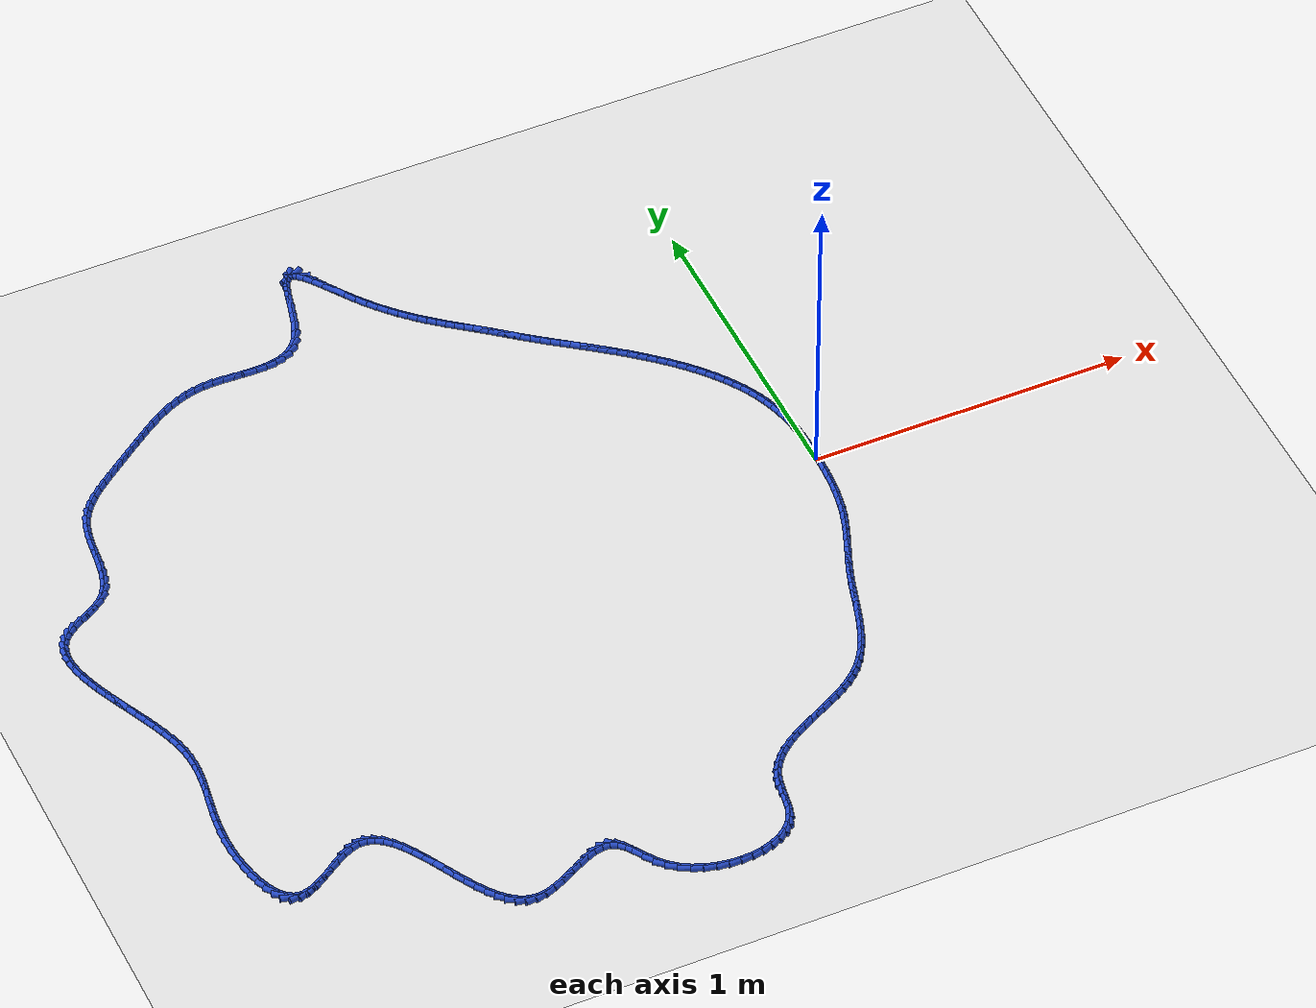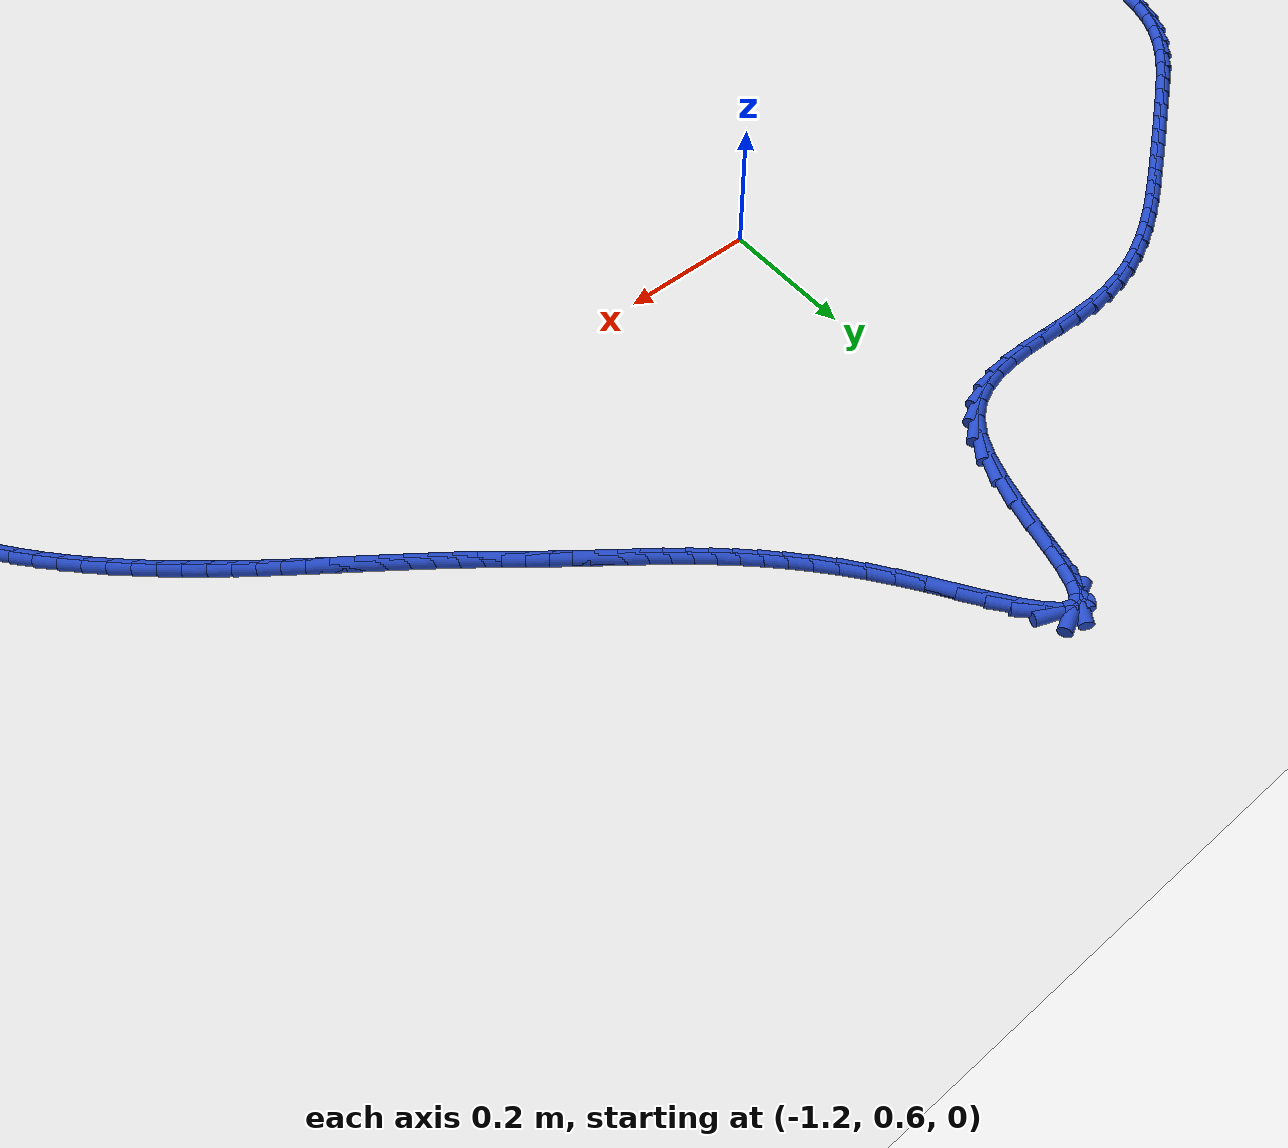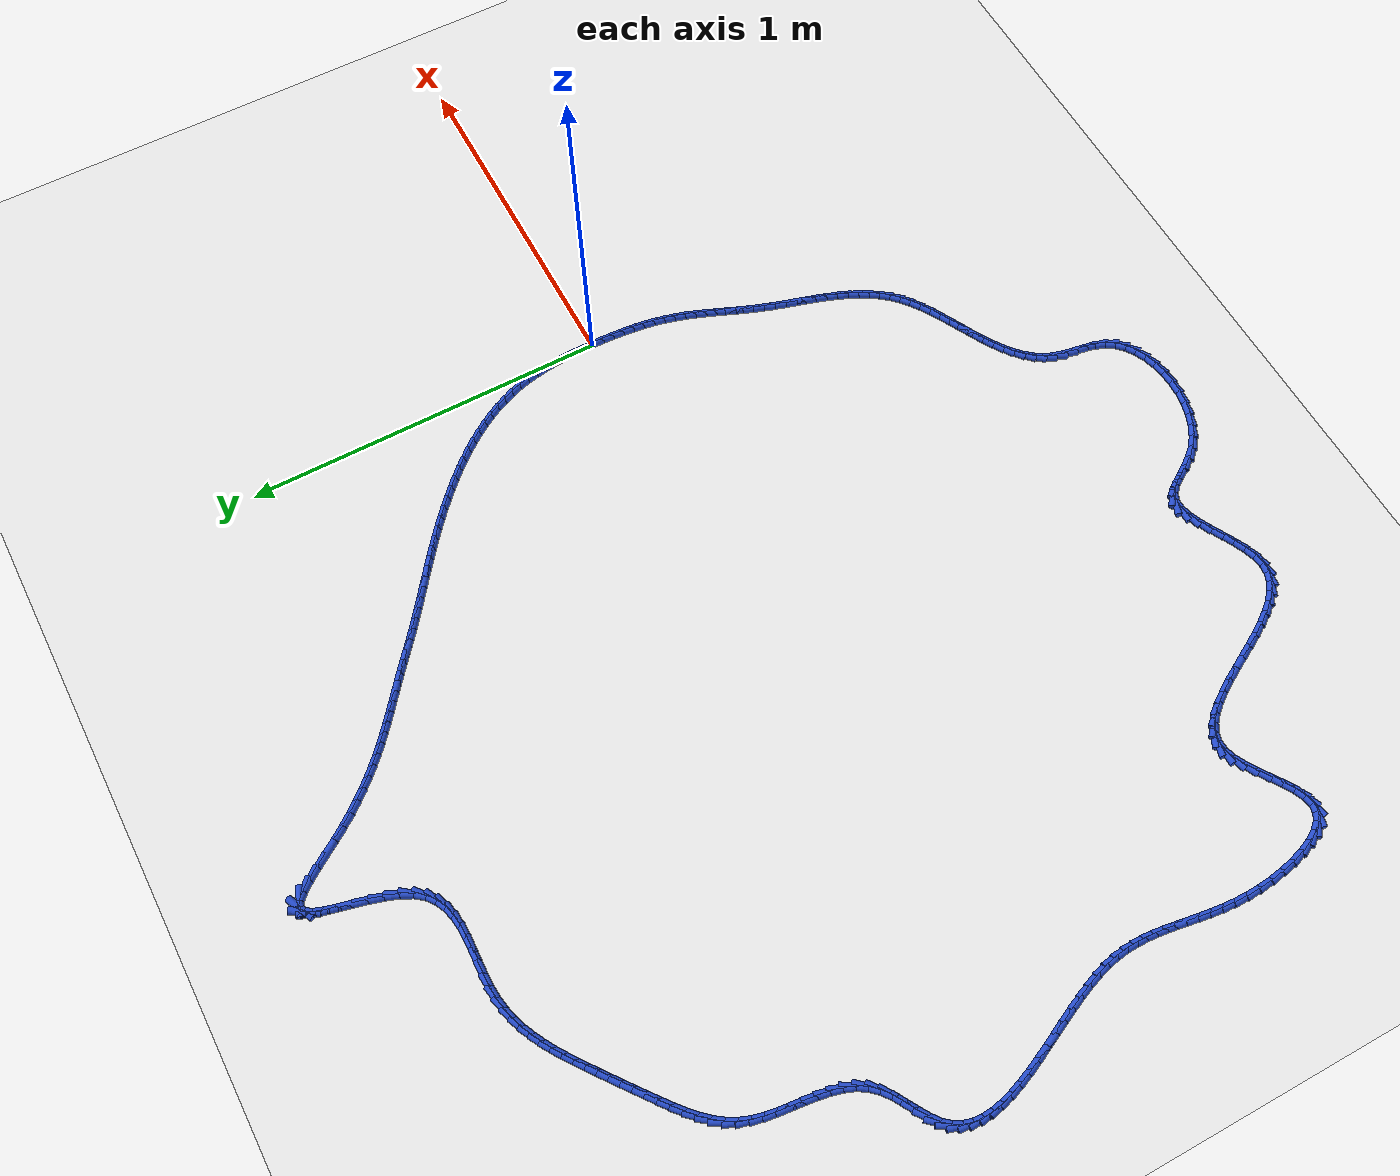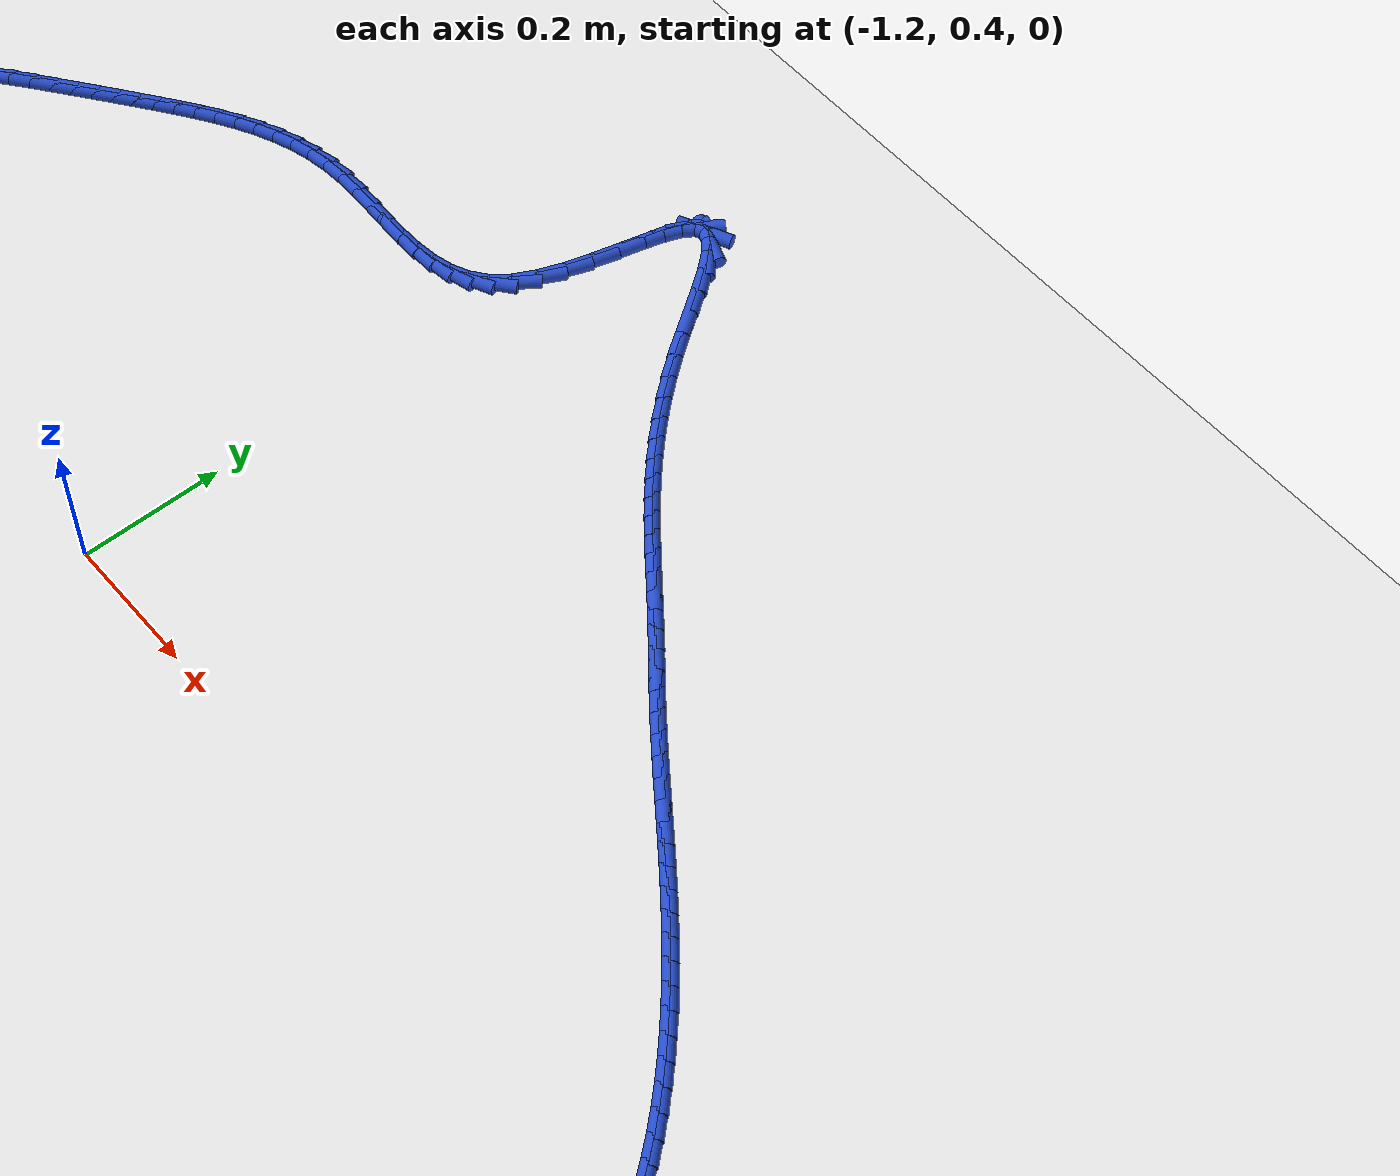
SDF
<sdf version="1.6">
 <world name="default">
  <light name="sun" type="directional">
   <pose>0 0 10 0 -0 0</pose>
   <diffuse>0.8 0.8 0.8 1</diffuse>
   <specular>0.2 0.2 0.2 1</specular>
   <attenuation>
    <range>1000</range>
    <constant>0.9</constant>
    <linear>0.01</linear>
    <quadratic>0.001</quadratic>
   </attenuation>
   <direction>-0.5 0.1 -0.9</direction>
  </light>
  <model name="ground_plane">
   <static>1</static>
   <link name="link">
    <collision name="collision">
     <geometry><plane><normal>0 0 1</normal><size>100 100</size></plane></geometry>
     <surface><friction><ode><mu>100</mu><mu2>50</mu2></ode></friction></surface>
    </collision>
    <visual name="visual">
     <cast_shadows>0</cast_shadows>
     <geometry><plane><normal>0 0 1</normal><size>100 100</size></plane></geometry>
     <material>
      <script><uri>file://media/materials/scripts/gazebo.material</uri><name>Gazebo/WhiteGlow</name></script>
     </material>
    </visual>
   </link>
  </model>
  <gravity>0 0 -9.8</gravity>
  <magnetic_field>6e-06 2.3e-05 -4.2e-05</magnetic_field>
  <atmosphere type="adiabatic"/>
  <physics name="default_physics" default="0" type="ode">
   <max_step_size>0.001</max_step_size>
   <real_time_factor>1</real_time_factor>
   <real_time_update_rate>1000</real_time_update_rate>
  </physics>
  <scene><ambient>0.4 0.4 0.4 1</ambient><background>0.7 0.7 0.7 1</background><shadows>1</shadows></scene>
  <spherical_coordinates>
   <surface_model>EARTH_WGS84</surface_model>
   <latitude_deg>0</latitude_deg>
   <longitude_deg>0</longitude_deg>
   <elevation>0</elevation>
   <heading_deg>0</heading_deg>
  </spherical_coordinates>
  <model name="line">
   <link name="link_0">
    <pose>-4.7704895589362195e-18 8.326672684688674e-17 0.01 0 1.57 -1.5682312444252402</pose>
    <collision name="collision">
     <geometry><cylinder><radius>0.01</radius><length>0.08</length></cylinder></geometry>
    </collision>
    <visual name="visual">
     <material>
      <script><name>Gazebo/Blue</name><uri>file://media/materials/scripts/gazebo.material</uri></script>
     </material>
     <geometry><cylinder><radius>0.01</radius><length>0.08</length></cylinder></geometry>
    </visual>
   </link>
   <link name="link_1">
    <pose>-7.850983834851156e-05 0.030607074099505506 0.01 0 1.57 -1.5445897610422592</pose>
    <collision name="collision">
     <geometry><cylinder><radius>0.01</radius><length>0.08</length></cylinder></geometry>
    </collision>
    <visual name="visual">
     <material>
      <script><name>Gazebo/Blue</name><uri>file://media/materials/scripts/gazebo.material</uri></script>
     </material>
     <geometry><cylinder><radius>0.01</radius><length>0.08</length></cylinder></geometry>
    </visual>
   </link>
   <link name="link_2">
    <pose>-0.0008796718463034315 0.06117111666339974 0.01 0 1.57 -1.5160301594730798</pose>
    <collision name="collision">
     <geometry><cylinder><radius>0.01</radius><length>0.08</length></cylinder></geometry>
    </collision>
    <visual name="visual">
     <material>
      <script><name>Gazebo/Blue</name><uri>file://media/materials/scripts/gazebo.material</uri></script>
     </material>
     <geometry><cylinder><radius>0.01</radius><length>0.08</length></cylinder></geometry>
    </visual>
   </link>
   <link name="link_3">
    <pose>-0.002548365899162327 0.09161008067350809 0.01 0 1.57 -1.48234289069405</pose>
    <collision name="collision">
     <geometry><cylinder><radius>0.01</radius><length>0.08</length></cylinder></geometry>
    </collision>
    <visual name="visual">
     <material>
      <script><name>Gazebo/Blue</name><uri>file://media/materials/scripts/gazebo.material</uri></script>
     </material>
     <geometry><cylinder><radius>0.01</radius><length>0.08</length></cylinder></geometry>
    </visual>
   </link>
   <link name="link_4">
    <pose>-0.005229471872222764 0.12184191911165575 0.01 0 1.57 -1.4433000936454674</pose>
    <collision name="collision">
     <geometry><cylinder><radius>0.01</radius><length>0.08</length></cylinder></geometry>
    </collision>
    <visual name="visual">
     <material>
      <script><name>Gazebo/Blue</name><uri>file://media/materials/scripts/gazebo.material</uri></script>
     </material>
     <geometry><cylinder><radius>0.01</radius><length>0.08</length></cylinder></geometry>
    </visual>
   </link>
   <link name="link_5">
    <pose>-0.009067869640782307 0.151784584959668 0.01 0 1.57 -1.3986807048463175</pose>
    <collision name="collision">
     <geometry><cylinder><radius>0.01</radius><length>0.08</length></cylinder></geometry>
    </collision>
    <visual name="visual">
     <material>
      <script><name>Gazebo/Blue</name><uri>file://media/materials/scripts/gazebo.material</uri></script>
     </material>
     <geometry><cylinder><radius>0.01</radius><length>0.08</length></cylinder></geometry>
    </visual>
   </link>
   <link name="link_6">
    <pose>-0.01420843908013852 0.18135603119937016 0.01 0 1.57 -1.3483044304760463</pose>
    <collision name="collision">
     <geometry><cylinder><radius>0.01</radius><length>0.08</length></cylinder></geometry>
    </collision>
    <visual name="visual">
     <material>
      <script><name>Gazebo/Blue</name><uri>file://media/materials/scripts/gazebo.material</uri></script>
     </material>
     <geometry><cylinder><radius>0.01</radius><length>0.08</length></cylinder></geometry>
    </visual>
   </link>
   <link name="link_7">
    <pose>-0.020796060065588963 0.21047421081258744 0.01 0 1.57 -1.2920756030313647</pose>
    <collision name="collision">
     <geometry><cylinder><radius>0.01</radius><length>0.08</length></cylinder></geometry>
    </collision>
    <visual name="visual">
     <material>
      <script><name>Gazebo/Blue</name><uri>file://media/materials/scripts/gazebo.material</uri></script>
     </material>
     <geometry><cylinder><radius>0.01</radius><length>0.08</length></cylinder></geometry>
    </visual>
   </link>
   <link name="link_8">
    <pose>-0.028975612472431207 0.23905707678114507 0.01 0 1.57 -1.2314656069206433</pose>
    <collision name="collision">
     <geometry><cylinder><radius>0.01</radius><length>0.08</length></cylinder></geometry>
    </collision>
    <visual name="visual">
     <material>
      <script><name>Gazebo/Blue</name><uri>file://media/materials/scripts/gazebo.material</uri></script>
     </material>
     <geometry><cylinder><radius>0.01</radius><length>0.08</length></cylinder></geometry>
    </visual>
   </link>
   <link name="link_9">
    <pose>-0.03885210006781969 0.2670370610846994 0.01 0 1.57 -1.1725634312426072</pose>
    <collision name="collision">
     <geometry><cylinder><radius>0.01</radius><length>0.08</length></cylinder></geometry>
    </collision>
    <visual name="visual">
     <material>
      <script><name>Gazebo/Blue</name><uri>file://media/materials/scripts/gazebo.material</uri></script>
     </material>
     <geometry><cylinder><radius>0.01</radius><length>0.08</length></cylinder></geometry>
    </visual>
   </link>
   <link name="link_10">
    <pose>-0.050366586759226124 0.29440612219591944 0.01 0 1.57 -1.1170991158874501</pose>
    <collision name="collision">
     <geometry><cylinder><radius>0.01</radius><length>0.08</length></cylinder></geometry>
    </collision>
    <visual name="visual">
     <material>
      <script><name>Gazebo/Blue</name><uri>file://media/materials/scripts/gazebo.material</uri></script>
     </material>
     <geometry><cylinder><radius>0.01</radius><length>0.08</length></cylinder></geometry>
    </visual>
   </link>
   <link name="link_11">
    <pose>-0.06341801197118578 0.32117151396923244 0.01 0 1.57 -1.0651887856976803</pose>
    <collision name="collision">
     <geometry><cylinder><radius>0.01</radius><length>0.08</length></cylinder></geometry>
    </collision>
    <visual name="visual">
     <material>
      <script><name>Gazebo/Blue</name><uri>file://media/materials/scripts/gazebo.material</uri></script>
     </material>
     <geometry><cylinder><radius>0.01</radius><length>0.08</length></cylinder></geometry>
    </visual>
   </link>
   <link name="link_12">
    <pose>-0.07790531509691316 0.3473404902704379 0.01 0 1.57 -1.0168564107348212</pose>
    <collision name="collision">
     <geometry><cylinder><radius>0.01</radius><length>0.08</length></cylinder></geometry>
    </collision>
    <visual name="visual">
     <material>
      <script><name>Gazebo/Blue</name><uri>file://media/materials/scripts/gazebo.material</uri></script>
     </material>
     <geometry><cylinder><radius>0.01</radius><length>0.08</length></cylinder></geometry>
    </visual>
   </link>
   <link name="link_13">
    <pose>-0.09372743552962286 0.37292030496533546 0.01 0 1.57 -0.9720539099214611</pose>
    <collision name="collision">
     <geometry><cylinder><radius>0.01</radius><length>0.08</length></cylinder></geometry>
    </collision>
    <visual name="visual">
     <material>
      <script><name>Gazebo/Blue</name><uri>file://media/materials/scripts/gazebo.material</uri></script>
     </material>
     <geometry><cylinder><radius>0.01</radius><length>0.08</length></cylinder></geometry>
    </visual>
   </link>
   <link name="link_14">
    <pose>-0.11078331266252939 0.39791821191972493 0.01 0 1.57 -0.9306806682658132</pose>
    <collision name="collision">
     <geometry><cylinder><radius>0.01</radius><length>0.08</length></cylinder></geometry>
    </collision>
    <visual name="visual">
     <material>
      <script><name>Gazebo/Blue</name><uri>file://media/materials/scripts/gazebo.material</uri></script>
     </material>
     <geometry><cylinder><radius>0.01</radius><length>0.08</length></cylinder></geometry>
    </visual>
   </link>
   <link name="link_15">
    <pose>-0.12897188588884728 0.4223414649994055 0.01 0 1.57 -0.8926009176055771</pose>
    <collision name="collision">
     <geometry><cylinder><radius>0.01</radius><length>0.08</length></cylinder></geometry>
    </collision>
    <visual name="visual">
     <material>
      <script><name>Gazebo/Blue</name><uri>file://media/materials/scripts/gazebo.material</uri></script>
     </material>
     <geometry><cylinder><radius>0.01</radius><length>0.08</length></cylinder></geometry>
    </visual>
   </link>
   <link name="link_16">
    <pose>-0.14819209460179109 0.4461973180701771 0.01 0 1.57 -0.8576582614860583</pose>
    <collision name="collision">
     <geometry><cylinder><radius>0.01</radius><length>0.08</length></cylinder></geometry>
    </collision>
    <visual name="visual">
     <material>
      <script><name>Gazebo/Blue</name><uri>file://media/materials/scripts/gazebo.material</uri></script>
     </material>
     <geometry><cylinder><radius>0.01</radius><length>0.08</length></cylinder></geometry>
    </visual>
   </link>
   <link name="link_17">
    <pose>-0.16834287819457538 0.4694930249978393 0.01 0 1.57 -0.825687221884039</pose>
    <collision name="collision">
     <geometry><cylinder><radius>0.01</radius><length>0.08</length></cylinder></geometry>
    </collision>
    <visual name="visual">
     <material>
      <script><name>Gazebo/Blue</name><uri>file://media/materials/scripts/gazebo.material</uri></script>
     </material>
     <geometry><cylinder><radius>0.01</radius><length>0.08</length></cylinder></geometry>
    </visual>
   </link>
   <link name="link_18">
    <pose>-0.1893231760604147 0.4922358396481916 0.01 0 1.57 -0.7965220499734265</pose>
    <collision name="collision">
     <geometry><cylinder><radius>0.01</radius><length>0.08</length></cylinder></geometry>
    </collision>
    <visual name="visual">
     <material>
      <script><name>Gazebo/Blue</name><uri>file://media/materials/scripts/gazebo.material</uri></script>
     </material>
     <geometry><cylinder><radius>0.01</radius><length>0.08</length></cylinder></geometry>
    </visual>
   </link>
   <link name="link_19">
    <pose>-0.2110319275925236 0.5144330158870337 0.01 0 1.57 -0.7700032238204607</pose>
    <collision name="collision">
     <geometry><cylinder><radius>0.01</radius><length>0.08</length></cylinder></geometry>
    </collision>
    <visual name="visual">
     <material>
      <script><name>Gazebo/Blue</name><uri>file://media/materials/scripts/gazebo.material</uri></script>
     </material>
     <geometry><cylinder><radius>0.01</radius><length>0.08</length></cylinder></geometry>
    </visual>
   </link>
   <link name="link_20">
    <pose>-0.2333680721841166 0.5360918075801652 0.01 0 1.57 -0.7459821125124565</pose>
    <collision name="collision">
     <geometry><cylinder><radius>0.01</radius><length>0.08</length></cylinder></geometry>
    </collision>
    <visual name="visual">
     <material>
      <script><name>Gazebo/Blue</name><uri>file://media/materials/scripts/gazebo.material</uri></script>
     </material>
     <geometry><cylinder><radius>0.01</radius><length>0.08</length></cylinder></geometry>
    </visual>
   </link>
   <link name="link_21">
    <pose>-0.25623054922840827 0.5572194685933857 0.01 0 1.57 -0.7243242707508456</pose>
    <collision name="collision">
     <geometry><cylinder><radius>0.01</radius><length>0.08</length></cylinder></geometry>
    </collision>
    <visual name="visual">
     <material>
      <script><name>Gazebo/Blue</name><uri>file://media/materials/scripts/gazebo.material</uri></script>
     </material>
     <geometry><cylinder><radius>0.01</radius><length>0.08</length></cylinder></geometry>
    </visual>
   </link>
   <link name="link_22">
    <pose>-0.2795182981186131 0.5778232527924949 0.01 0 1.57 -0.7049117784476686</pose>
    <collision name="collision">
     <geometry><cylinder><radius>0.01</radius><length>0.08</length></cylinder></geometry>
    </collision>
    <visual name="visual">
     <material>
      <script><name>Gazebo/Blue</name><uri>file://media/materials/scripts/gazebo.material</uri></script>
     </material>
     <geometry><cylinder><radius>0.01</radius><length>0.08</length></cylinder></geometry>
    </visual>
   </link>
   <link name="link_23">
    <pose>-0.3031302582479457 0.597910414043292 0.01 0 1.57 -0.6876449810688887</pose>
    <collision name="collision">
     <geometry><cylinder><radius>0.01</radius><length>0.08</length></cylinder></geometry>
    </collision>
    <visual name="visual">
     <material>
      <script><name>Gazebo/Blue</name><uri>file://media/materials/scripts/gazebo.material</uri></script>
     </material>
     <geometry><cylinder><radius>0.01</radius><length>0.08</length></cylinder></geometry>
    </visual>
   </link>
   <link name="link_24">
    <pose>-0.3269653690096206 0.6174882062115772 0.01 0 1.57 -0.6724533190993339</pose>
    <collision name="collision">
     <geometry><cylinder><radius>0.01</radius><length>0.08</length></cylinder></geometry>
    </collision>
    <visual name="visual">
     <material>
      <script><name>Gazebo/Blue</name><uri>file://media/materials/scripts/gazebo.material</uri></script>
     </material>
     <geometry><cylinder><radius>0.01</radius><length>0.08</length></cylinder></geometry>
    </visual>
   </link>
   <link name="link_25">
    <pose>-0.35092402292409525 0.6365654076581861 0.01 0 1.57 -0.6595555227948436</pose>
    <collision name="collision">
     <geometry><cylinder><radius>0.01</radius><length>0.08</length></cylinder></geometry>
    </collision>
    <visual name="visual">
     <material>
      <script><name>Gazebo/Blue</name><uri>file://media/materials/scripts/gazebo.material</uri></script>
     </material>
     <geometry><cylinder><radius>0.01</radius><length>0.08</length></cylinder></geometry>
    </visual>
   </link>
   <link name="link_26">
    <pose>-0.37494512602725527 0.6551912017830771 0.01 0 1.57 -0.6493044399021799</pose>
    <collision name="collision">
     <geometry><cylinder><radius>0.01</radius><length>0.08</length></cylinder></geometry>
    </collision>
    <visual name="visual">
     <material>
      <script><name>Gazebo/Blue</name><uri>file://media/materials/scripts/gazebo.material</uri></script>
     </material>
     <geometry><cylinder><radius>0.01</radius><length>0.08</length></cylinder></geometry>
    </visual>
   </link>
   <link name="link_27">
    <pose>-0.39900915874694404 0.6734583882314369 0.01 0 1.57 -0.641809652778201</pose>
    <collision name="collision">
     <geometry><cylinder><radius>0.01</radius><length>0.08</length></cylinder></geometry>
    </collision>
    <visual name="visual">
     <material>
      <script><name>Gazebo/Blue</name><uri>file://media/materials/scripts/gazebo.material</uri></script>
     </material>
     <geometry><cylinder><radius>0.01</radius><length>0.08</length></cylinder></geometry>
    </visual>
   </link>
   <link name="link_28">
    <pose>-0.4230986679361195 0.6914619345624093 0.01 0 1.57 -0.6371427167157656</pose>
    <collision name="collision">
     <geometry><cylinder><radius>0.01</radius><length>0.08</length></cylinder></geometry>
    </collision>
    <visual name="visual">
     <material>
      <script><name>Gazebo/Blue</name><uri>file://media/materials/scripts/gazebo.material</uri></script>
     </material>
     <geometry><cylinder><radius>0.01</radius><length>0.08</length></cylinder></geometry>
    </visual>
   </link>
   <link name="link_29">
    <pose>-0.4471962004477398 0.7092968083351378 0.01 0 1.57 -0.6353506193693912</pose>
    <collision name="collision">
     <geometry><cylinder><radius>0.01</radius><length>0.08</length></cylinder></geometry>
    </collision>
    <visual name="visual">
     <material>
      <script><name>Gazebo/Blue</name><uri>file://media/materials/scripts/gazebo.material</uri></script>
     </material>
     <geometry><cylinder><radius>0.01</radius><length>0.08</length></cylinder></geometry>
    </visual>
   </link>
   <link name="link_30">
    <pose>-0.4712843031347625 0.7270579771087652 0.01 0 1.57 -0.636455844635083</pose>
    <collision name="collision">
     <geometry><cylinder><radius>0.01</radius><length>0.08</length></cylinder></geometry>
    </collision>
    <visual name="visual">
     <material>
      <script><name>Gazebo/Blue</name><uri>file://media/materials/scripts/gazebo.material</uri></script>
     </material>
     <geometry><cylinder><radius>0.01</radius><length>0.08</length></cylinder></geometry>
    </visual>
   </link>
   <link name="link_31">
    <pose>-0.4953455228501458 0.7448404084424349 0.01 0 1.57 -0.6404562847046027</pose>
    <collision name="collision">
     <geometry><cylinder><radius>0.01</radius><length>0.08</length></cylinder></geometry>
    </collision>
    <visual name="visual">
     <material>
      <script><name>Gazebo/Blue</name><uri>file://media/materials/scripts/gazebo.material</uri></script>
     </material>
     <geometry><cylinder><radius>0.01</radius><length>0.08</length></cylinder></geometry>
    </visual>
   </link>
   <link name="link_32">
    <pose>-0.5193624064468474 0.7627390698952904 0.01 0 1.57 -0.6473249576548522</pose>
    <collision name="collision">
     <geometry><cylinder><radius>0.01</radius><length>0.08</length></cylinder></geometry>
    </collision>
    <visual name="visual">
     <material>
      <script><name>Gazebo/Blue</name><uri>file://media/materials/scripts/gazebo.material</uri></script>
     </material>
     <geometry><cylinder><radius>0.01</radius><length>0.08</length></cylinder></geometry>
    </visual>
   </link>
   <link name="link_33">
    <pose>-0.5433175007778254 0.7808489290264747 0.01 0 1.57 -0.6570095521813457</pose>
    <collision name="collision">
     <geometry><cylinder><radius>0.01</radius><length>0.08</length></cylinder></geometry>
    </collision>
    <visual name="visual">
     <material>
      <script><name>Gazebo/Blue</name><uri>file://media/materials/scripts/gazebo.material</uri></script>
     </material>
     <geometry><cylinder><radius>0.01</radius><length>0.08</length></cylinder></geometry>
    </visual>
   </link>
   <link name="link_34">
    <pose>-0.5671933526960378 0.7992649533951315 0.01 0 1.57 -0.6689239229753259</pose>
    <collision name="collision">
     <geometry><cylinder><radius>0.01</radius><length>0.08</length></cylinder></geometry>
    </collision>
    <visual name="visual">
     <material>
      <script><name>Gazebo/Blue</name><uri>file://media/materials/scripts/gazebo.material</uri></script>
     </material>
     <geometry><cylinder><radius>0.01</radius><length>0.08</length></cylinder></geometry>
    </visual>
   </link>
   <link name="link_35">
    <pose>-0.5909693851962724 0.818060006262623 0.01 0 1.57 -0.6774498926883321</pose>
    <collision name="collision">
     <geometry><cylinder><radius>0.01</radius><length>0.08</length></cylinder></geometry>
    </collision>
    <visual name="visual">
     <material>
      <script><name>Gazebo/Blue</name><uri>file://media/materials/scripts/gazebo.material</uri></script>
     </material>
     <geometry><cylinder><radius>0.01</radius><length>0.08</length></cylinder></geometry>
    </visual>
   </link>
   <link name="link_36">
    <pose>-0.6145904023506027 0.8370619887521809 0.01 0 1.57 -0.6792319518733971</pose>
    <collision name="collision">
     <geometry><cylinder><radius>0.01</radius><length>0.08</length></cylinder></geometry>
    </collision>
    <visual name="visual">
     <material>
      <script><name>Gazebo/Blue</name><uri>file://media/materials/scripts/gazebo.material</uri></script>
     </material>
     <geometry><cylinder><radius>0.01</radius><length>0.08</length></cylinder></geometry>
    </visual>
   </link>
   <link name="link_37">
    <pose>-0.6379796532220209 0.8559462795889359 0.01 0 1.57 -0.6741317918165386</pose>
    <collision name="collision">
     <geometry><cylinder><radius>0.01</radius><length>0.08</length></cylinder></geometry>
    </collision>
    <visual name="visual">
     <material>
      <script><name>Gazebo/Blue</name><uri>file://media/materials/scripts/gazebo.material</uri></script>
     </material>
     <geometry><cylinder><radius>0.01</radius><length>0.08</length></cylinder></geometry>
    </visual>
   </link>
   <link name="link_38">
    <pose>-0.6610604841177483 0.8743878976298244 0.01 0 1.57 -0.6656646762208325</pose>
    <collision name="collision">
     <geometry><cylinder><radius>0.01</radius><length>0.08</length></cylinder></geometry>
    </collision>
    <visual name="visual">
     <material>
      <script><name>Gazebo/Blue</name><uri>file://media/materials/scripts/gazebo.material</uri></script>
     </material>
     <geometry><cylinder><radius>0.01</radius><length>0.08</length></cylinder></geometry>
    </visual>
   </link>
   <link name="link_39">
    <pose>-0.6837948518364323 0.8922394192829913 0.01 0 1.57 -0.6608908706929832</pose>
    <collision name="collision">
     <geometry><cylinder><radius>0.01</radius><length>0.08</length></cylinder></geometry>
    </collision>
    <visual name="visual">
     <material>
      <script><name>Gazebo/Blue</name><uri>file://media/materials/scripts/gazebo.material</uri></script>
     </material>
     <geometry><cylinder><radius>0.01</radius><length>0.08</length></cylinder></geometry>
    </visual>
   </link>
   <link name="link_40">
    <pose>-0.7062137398512681 0.9096708530028464 0.01 0 1.57 -0.6608479817907046</pose>
    <collision name="collision">
     <geometry><cylinder><radius>0.01</radius><length>0.08</length></cylinder></geometry>
    </collision>
    <visual name="visual">
     <material>
      <script><name>Gazebo/Blue</name><uri>file://media/materials/scripts/gazebo.material</uri></script>
     </material>
     <geometry><cylinder><radius>0.01</radius><length>0.08</length></cylinder></geometry>
    </visual>
   </link>
   <link name="link_41">
    <pose>-0.7283552892869082 0.9268851230399509 0.01 0 1.57 -0.6657162424116385</pose>
    <collision name="collision">
     <geometry><cylinder><radius>0.01</radius><length>0.08</length></cylinder></geometry>
    </collision>
    <visual name="visual">
     <material>
      <script><name>Gazebo/Blue</name><uri>file://media/materials/scripts/gazebo.material</uri></script>
     </material>
     <geometry><cylinder><radius>0.01</radius><length>0.08</length></cylinder></geometry>
    </visual>
   </link>
   <link name="link_42">
    <pose>-0.7502576412680043 0.9440851536448641 0.01 0 1.57 -0.675518171484937</pose>
    <collision name="collision">
     <geometry><cylinder><radius>0.01</radius><length>0.08</length></cylinder></geometry>
    </collision>
    <visual name="visual">
     <material>
      <script><name>Gazebo/Blue</name><uri>file://media/materials/scripts/gazebo.material</uri></script>
     </material>
     <geometry><cylinder><radius>0.01</radius><length>0.08</length></cylinder></geometry>
    </visual>
   </link>
   <link name="link_43">
    <pose>-0.7719589369192088 0.9614738690681471 0.01 0 1.57 -0.690108288395644</pose>
    <collision name="collision">
     <geometry><cylinder><radius>0.01</radius><length>0.08</length></cylinder></geometry>
    </collision>
    <visual name="visual">
     <material>
      <script><name>Gazebo/Blue</name><uri>file://media/materials/scripts/gazebo.material</uri></script>
     </material>
     <geometry><cylinder><radius>0.01</radius><length>0.08</length></cylinder></geometry>
    </visual>
   </link>
   <link name="link_44">
    <pose>-0.793497317365173 0.9792541935603594 0.01 0 1.57 -0.7091735315733255</pose>
    <collision name="collision">
     <geometry><cylinder><radius>0.01</radius><length>0.08</length></cylinder></geometry>
    </collision>
    <visual name="visual">
     <material>
      <script><name>Gazebo/Blue</name><uri>file://media/materials/scripts/gazebo.material</uri></script>
     </material>
     <geometry><cylinder><radius>0.01</radius><length>0.08</length></cylinder></geometry>
    </visual>
   </link>
   <link name="link_45">
    <pose>-0.8149109237305493 0.9976290513720613 0.01 0 1.57 -0.7322459075564292</pose>
    <collision name="collision">
     <geometry><cylinder><radius>0.01</radius><length>0.08</length></cylinder></geometry>
    </collision>
    <visual name="visual">
     <material>
      <script><name>Gazebo/Blue</name><uri>file://media/materials/scripts/gazebo.material</uri></script>
     </material>
     <geometry><cylinder><radius>0.01</radius><length>0.08</length></cylinder></geometry>
    </visual>
   </link>
   <link name="link_46">
    <pose>-0.8362378971399903 1.0168013667538136 0.01 0 1.57 -0.7587276992665093</pose>
    <collision name="collision">
     <geometry><cylinder><radius>0.01</radius><length>0.08</length></cylinder></geometry>
    </collision>
    <visual name="visual">
     <material>
      <script><name>Gazebo/Blue</name><uri>file://media/materials/scripts/gazebo.material</uri></script>
     </material>
     <geometry><cylinder><radius>0.01</radius><length>0.08</length></cylinder></geometry>
    </visual>
   </link>
   <link name="link_47">
    <pose>-0.8575163787181472 1.0369740639561762 0.01 0 1.57 -0.787927753318429</pose>
    <collision name="collision">
     <geometry><cylinder><radius>0.01</radius><length>0.08</length></cylinder></geometry>
    </collision>
    <visual name="visual">
     <material>
      <script><name>Gazebo/Blue</name><uri>file://media/materials/scripts/gazebo.material</uri></script>
     </material>
     <geometry><cylinder><radius>0.01</radius><length>0.08</length></cylinder></geometry>
    </visual>
   </link>
   <link name="link_48">
    <pose>-0.8787845095896724 1.0583500672297093 0.01 0 1.57 -0.8191053220693056</pose>
    <collision name="collision">
     <geometry><cylinder><radius>0.01</radius><length>0.08</length></cylinder></geometry>
    </collision>
    <visual name="visual">
     <material>
      <script><name>Gazebo/Blue</name><uri>file://media/materials/scripts/gazebo.material</uri></script>
     </material>
     <geometry><cylinder><radius>0.01</radius><length>0.08</length></cylinder></geometry>
    </visual>
   </link>
   <link name="link_49">
    <pose>-0.9000804308792181 1.0811323008249736 0.01 0 1.57 -0.8515163079065063</pose>
    <collision name="collision">
     <geometry><cylinder><radius>0.01</radius><length>0.08</length></cylinder></geometry>
    </collision>
    <visual name="visual">
     <material>
      <script><name>Gazebo/Blue</name><uri>file://media/materials/scripts/gazebo.material</uri></script>
     </material>
     <geometry><cylinder><radius>0.01</radius><length>0.08</length></cylinder></geometry>
    </visual>
   </link>
   <link name="link_50">
    <pose>-0.9214422837114359 1.1055236889925286 0.01 0 1.57 -0.8844561837108461</pose>
    <collision name="collision">
     <geometry><cylinder><radius>0.01</radius><length>0.08</length></cylinder></geometry>
    </collision>
    <visual name="visual">
     <material>
      <script><name>Gazebo/Blue</name><uri>file://media/materials/scripts/gazebo.material</uri></script>
     </material>
     <geometry><cylinder><radius>0.01</radius><length>0.08</length></cylinder></geometry>
    </visual>
   </link>
   <link name="link_51">
    <pose>-0.9429082092109784 1.1317271559829356 0.01 0 1.57 -0.9172946285322058</pose>
    <collision name="collision">
     <geometry><cylinder><radius>0.01</radius><length>0.08</length></cylinder></geometry>
    </collision>
    <visual name="visual">
     <material>
      <script><name>Gazebo/Blue</name><uri>file://media/materials/scripts/gazebo.material</uri></script>
     </material>
     <geometry><cylinder><radius>0.01</radius><length>0.08</length></cylinder></geometry>
    </visual>
   </link>
   <link name="link_52">
    <pose>-0.9645163485024972 1.159945626046754 0.01 0 1.57 -0.9494392291946072</pose>
    <collision name="collision">
     <geometry><cylinder><radius>0.01</radius><length>0.08</length></cylinder></geometry>
    </collision>
    <visual name="visual">
     <material>
      <script><name>Gazebo/Blue</name><uri>file://media/materials/scripts/gazebo.material</uri></script>
     </material>
     <geometry><cylinder><radius>0.01</radius><length>0.08</length></cylinder></geometry>
    </visual>
   </link>
   <link name="link_53">
    <pose>-0.9863037821084302 1.1903767128958613 0.01 0 1.57 -0.9726581120592046</pose>
    <collision name="collision">
     <geometry><cylinder><radius>0.01</radius><length>0.08</length></cylinder></geometry>
    </collision>
    <visual name="visual">
     <material>
      <script><name>Gazebo/Blue</name><uri>file://media/materials/scripts/gazebo.material</uri></script>
     </material>
     <geometry><cylinder><radius>0.01</radius><length>0.08</length></cylinder></geometry>
    </visual>
   </link>
   <link name="link_54">
    <pose>-1.0081523176206042 1.22244056354093 0.01 0 1.57 -0.9728607349225045</pose>
    <collision name="collision">
     <geometry><cylinder><radius>0.01</radius><length>0.08</length></cylinder></geometry>
    </collision>
    <visual name="visual">
     <material>
      <script><name>Gazebo/Blue</name><uri>file://media/materials/scripts/gazebo.material</uri></script>
     </material>
     <geometry><cylinder><radius>0.01</radius><length>0.08</length></cylinder></geometry>
    </visual>
   </link>
   <link name="link_55">
    <pose>-1.0296264994319848 1.2539687572258116 0.01 0 1.57 -0.9464987159668877</pose>
    <collision name="collision">
     <geometry><cylinder><radius>0.01</radius><length>0.08</length></cylinder></geometry>
    </collision>
    <visual name="visual">
     <material>
      <script><name>Gazebo/Blue</name><uri>file://media/materials/scripts/gazebo.material</uri></script>
     </material>
     <geometry><cylinder><radius>0.01</radius><length>0.08</length></cylinder></geometry>
    </visual>
   </link>
   <link name="link_56">
    <pose>-1.0502521292638136 1.2825988848599883 0.01 0 1.57 -0.8804130898124927</pose>
    <collision name="collision">
     <geometry><cylinder><radius>0.01</radius><length>0.08</length></cylinder></geometry>
    </collision>
    <visual name="visual">
     <material>
      <script><name>Gazebo/Blue</name><uri>file://media/materials/scripts/gazebo.material</uri></script>
     </material>
     <geometry><cylinder><radius>0.01</radius><length>0.08</length></cylinder></geometry>
    </visual>
   </link>
   <link name="link_57">
    <pose>-1.0695550088373322 1.3059685373529442 0.01 0 1.57 -0.7325445775962433</pose>
    <collision name="collision">
     <geometry><cylinder><radius>0.01</radius><length>0.08</length></cylinder></geometry>
    </collision>
    <visual name="visual">
     <material>
      <script><name>Gazebo/Blue</name><uri>file://media/materials/scripts/gazebo.material</uri></script>
     </material>
     <geometry><cylinder><radius>0.01</radius><length>0.08</length></cylinder></geometry>
    </visual>
   </link>
   <link name="link_58">
    <pose>-1.0870609398737816 1.3217153056141613 0.01 0 1.57 -0.36155479168169574</pose>
    <collision name="collision">
     <geometry><cylinder><radius>0.01</radius><length>0.08</length></cylinder></geometry>
    </collision>
    <visual name="visual">
     <material>
      <script><name>Gazebo/Blue</name><uri>file://media/materials/scripts/gazebo.material</uri></script>
     </material>
     <geometry><cylinder><radius>0.01</radius><length>0.08</length></cylinder></geometry>
    </visual>
   </link>
   <link name="link_59">
    <pose>-1.1022957240944031 1.327476780553123 0.01 0 1.57 0.43754772666090874</pose>
    <collision name="collision">
     <geometry><cylinder><radius>0.01</radius><length>0.08</length></cylinder></geometry>
    </collision>
    <visual name="visual">
     <material>
      <script><name>Gazebo/Blue</name><uri>file://media/materials/scripts/gazebo.material</uri></script>
     </material>
     <geometry><cylinder><radius>0.01</radius><length>0.08</length></cylinder></geometry>
    </visual>
   </link>
   <link name="link_60">
    <pose>-1.1149598095194417 1.3215526708953877 0.01 0 1.57 0.9961798162274388</pose>
    <collision name="collision">
     <geometry><cylinder><radius>0.01</radius><length>0.08</length></cylinder></geometry>
    </collision>
    <visual name="visual">
     <material>
      <script><name>Gazebo/Blue</name><uri>file://media/materials/scripts/gazebo.material</uri></script>
     </material>
     <geometry><cylinder><radius>0.01</radius><length>0.08</length></cylinder></geometry>
    </visual>
   </link>
   <link name="link_61">
    <pose>-1.1255378866109333 1.3052158997763992 0.01 0 1.57 1.2135944216616026</pose>
    <collision name="collision">
     <geometry><cylinder><radius>0.01</radius><length>0.08</length></cylinder></geometry>
    </collision>
    <visual name="visual">
     <material>
      <script><name>Gazebo/Blue</name><uri>file://media/materials/scripts/gazebo.material</uri></script>
     </material>
     <geometry><cylinder><radius>0.01</radius><length>0.08</length></cylinder></geometry>
    </visual>
   </link>
   <link name="link_62">
    <pose>-1.1347346830041112 1.2805735937095395 0.01 0 1.57 1.301252739196086</pose>
    <collision name="collision">
     <geometry><cylinder><radius>0.01</radius><length>0.08</length></cylinder></geometry>
    </collision>
    <visual name="visual">
     <material>
      <script><name>Gazebo/Blue</name><uri>file://media/materials/scripts/gazebo.material</uri></script>
     </material>
     <geometry><cylinder><radius>0.01</radius><length>0.08</length></cylinder></geometry>
    </visual>
   </link>
   <link name="link_63">
    <pose>-1.1432549375651893 1.2497329217870048 0.01 0 1.57 1.3307952499017193</pose>
    <collision name="collision">
     <geometry><cylinder><radius>0.01</radius><length>0.08</length></cylinder></geometry>
    </collision>
    <visual name="visual">
     <material>
      <script><name>Gazebo/Blue</name><uri>file://media/materials/scripts/gazebo.material</uri></script>
     </material>
     <geometry><cylinder><radius>0.01</radius><length>0.08</length></cylinder></geometry>
    </visual>
   </link>
   <link name="link_64">
    <pose>-1.1518033891603818 1.2148010531009907 0.01 0 1.57 1.3244818228559845</pose>
    <collision name="collision">
     <geometry><cylinder><radius>0.01</radius><length>0.08</length></cylinder></geometry>
    </collision>
    <visual name="visual">
     <material>
      <script><name>Gazebo/Blue</name><uri>file://media/materials/scripts/gazebo.material</uri></script>
     </material>
     <geometry><cylinder><radius>0.01</radius><length>0.08</length></cylinder></geometry>
    </visual>
   </link>
   <link name="link_65">
    <pose>-1.1610847766559025 1.1778851567436937 0.01 0 1.57 1.2873067813841286</pose>
    <collision name="collision">
     <geometry><cylinder><radius>0.01</radius><length>0.08</length></cylinder></geometry>
    </collision>
    <visual name="visual">
     <material>
      <script><name>Gazebo/Blue</name><uri>file://media/materials/scripts/gazebo.material</uri></script>
     </material>
     <geometry><cylinder><radius>0.01</radius><length>0.08</length></cylinder></geometry>
    </visual>
   </link>
   <link name="link_66">
    <pose>-1.171803838917966 1.141092401807309 0.01 0 1.57 1.2145504577317052</pose>
    <collision name="collision">
     <geometry><cylinder><radius>0.01</radius><length>0.08</length></cylinder></geometry>
    </collision>
    <visual name="visual">
     <material>
      <script><name>Gazebo/Blue</name><uri>file://media/materials/scripts/gazebo.material</uri></script>
     </material>
     <geometry><cylinder><radius>0.01</radius><length>0.08</length></cylinder></geometry>
    </visual>
   </link>
   <link name="link_67">
    <pose>-1.1846653148127853 1.106529957384032 0.01 0 1.57 1.0914946060567545</pose>
    <collision name="collision">
     <geometry><cylinder><radius>0.01</radius><length>0.08</length></cylinder></geometry>
    </collision>
    <visual name="visual">
     <material>
      <script><name>Gazebo/Blue</name><uri>file://media/materials/scripts/gazebo.material</uri></script>
     </material>
     <geometry><cylinder><radius>0.01</radius><length>0.08</length></cylinder></geometry>
    </visual>
   </link>
   <link name="link_68">
    <pose>-1.2003739432065752 1.07630499256606 0.01 0 1.57 0.894401758928169</pose>
    <collision name="collision">
     <geometry><cylinder><radius>0.01</radius><length>0.08</length></cylinder></geometry>
    </collision>
    <visual name="visual">
     <material>
      <script><name>Gazebo/Blue</name><uri>file://media/materials/scripts/gazebo.material</uri></script>
     </material>
     <geometry><cylinder><radius>0.01</radius><length>0.08</length></cylinder></geometry>
    </visual>
   </link>
   <link name="link_69">
    <pose>-1.2195786612807185 1.0523803055566108 0.01 0 1.57 0.6548795436853955</pose>
    <collision name="collision">
     <geometry><cylinder><radius>0.01</radius><length>0.08</length></cylinder></geometry>
    </collision>
    <visual name="visual">
     <material>
      <script><name>Gazebo/Blue</name><uri>file://media/materials/scripts/gazebo.material</uri></script>
     </material>
     <geometry><cylinder><radius>0.01</radius><length>0.08</length></cylinder></geometry>
    </visual>
   </link>
   <link name="link_70">
    <pose>-1.2422520066358196 1.0349687042301754 0.01 0 1.57 0.43255327784331943</pose>
    <collision name="collision">
     <geometry><cylinder><radius>0.01</radius><length>0.08</length></cylinder></geometry>
    </collision>
    <visual name="visual">
     <material>
      <script><name>Gazebo/Blue</name><uri>file://media/materials/scripts/gazebo.material</uri></script>
     </material>
     <geometry><cylinder><radius>0.01</radius><length>0.08</length></cylinder></geometry>
    </visual>
   </link>
   <link name="link_71">
    <pose>-1.2679166039188963 1.0231189754595804 0.01 0 1.57 0.252232687854796</pose>
    <collision name="collision">
     <geometry><cylinder><radius>0.01</radius><length>0.08</length></cylinder></geometry>
    </collision>
    <visual name="visual">
     <material>
      <script><name>Gazebo/Blue</name><uri>file://media/materials/scripts/gazebo.material</uri></script>
     </material>
     <geometry><cylinder><radius>0.01</radius><length>0.08</length></cylinder></geometry>
    </visual>
   </link>
   <link name="link_72">
    <pose>-1.2960869474237429 1.0158588711556031 0.01 0 1.57 0.12007728792528266</pose>
    <collision name="collision">
     <geometry><cylinder><radius>0.01</radius><length>0.08</length></cylinder></geometry>
    </collision>
    <visual name="visual">
     <material>
      <script><name>Gazebo/Blue</name><uri>file://media/materials/scripts/gazebo.material</uri></script>
     </material>
     <geometry><cylinder><radius>0.01</radius><length>0.08</length></cylinder></geometry>
    </visual>
   </link>
   <link name="link_73">
    <pose>-1.3262775314441533 1.012216143229021 0.01 0 1.57 0.03143454714573315</pose>
    <collision name="collision">
     <geometry><cylinder><radius>0.01</radius><length>0.08</length></cylinder></geometry>
    </collision>
    <visual name="visual">
     <material>
      <script><name>Gazebo/Blue</name><uri>file://media/materials/scripts/gazebo.material</uri></script>
     </material>
     <geometry><cylinder><radius>0.01</radius><length>0.08</length></cylinder></geometry>
    </visual>
   </link>
   <link name="link_74">
    <pose>-1.358002850273922 1.0112185435906111 0.01 0 1.57 -0.020600895250472435</pose>
    <collision name="collision">
     <geometry><cylinder><radius>0.01</radius><length>0.08</length></cylinder></geometry>
    </collision>
    <visual name="visual">
     <material>
      <script><name>Gazebo/Blue</name><uri>file://media/materials/scripts/gazebo.material</uri></script>
     </material>
     <geometry><cylinder><radius>0.01</radius><length>0.08</length></cylinder></geometry>
    </visual>
   </link>
   <link name="link_75">
    <pose>-1.3907773982068434 1.0118938241511506 0.01 0 1.57 -0.04124785741703648</pose>
    <collision name="collision">
     <geometry><cylinder><radius>0.01</radius><length>0.08</length></cylinder></geometry>
    </collision>
    <visual name="visual">
     <material>
      <script><name>Gazebo/Blue</name><uri>file://media/materials/scripts/gazebo.material</uri></script>
     </material>
     <geometry><cylinder><radius>0.01</radius><length>0.08</length></cylinder></geometry>
    </visual>
   </link>
   <link name="link_76">
    <pose>-1.4241156695367105 1.0132697368214176 0.01 0 1.57 -0.03303443889784161</pose>
    <collision name="collision">
     <geometry><cylinder><radius>0.01</radius><length>0.08</length></cylinder></geometry>
    </collision>
    <visual name="visual">
     <material>
      <script><name>Gazebo/Blue</name><uri>file://media/materials/scripts/gazebo.material</uri></script>
     </material>
     <geometry><cylinder><radius>0.01</radius><length>0.08</length></cylinder></geometry>
    </visual>
   </link>
   <link name="link_77">
    <pose>-1.4575321585573175 1.0143740335121885 0.01 0 1.57 0.004228110406147609</pose>
    <collision name="collision">
     <geometry><cylinder><radius>0.01</radius><length>0.08</length></cylinder></geometry>
    </collision>
    <visual name="visual">
     <material>
      <script><name>Gazebo/Blue</name><uri>file://media/materials/scripts/gazebo.material</uri></script>
     </material>
     <geometry><cylinder><radius>0.01</radius><length>0.08</length></cylinder></geometry>
    </visual>
   </link>
   <link name="link_78">
    <pose>-1.4905413595624601 1.0142344661342408 0.01 0 1.57 0.0732081177433576</pose>
    <collision name="collision">
     <geometry><cylinder><radius>0.01</radius><length>0.08</length></cylinder></geometry>
    </collision>
    <visual name="visual">
     <material>
      <script><name>Gazebo/Blue</name><uri>file://media/materials/scripts/gazebo.material</uri></script>
     </material>
     <geometry><cylinder><radius>0.01</radius><length>0.08</length></cylinder></geometry>
    </visual>
   </link>
   <link name="link_79">
    <pose>-1.5226578954262924 1.011879065624117 0.01 0 1.57 0.1683773865735783</pose>
    <collision name="collision">
     <geometry><cylinder><radius>0.01</radius><length>0.08</length></cylinder></geometry>
    </collision>
    <visual name="visual">
     <material>
      <script><name>Gazebo/Blue</name><uri>file://media/materials/scripts/gazebo.material</uri></script>
     </material>
     <geometry><cylinder><radius>0.01</radius><length>0.08</length></cylinder></geometry>
    </visual>
   </link>
   <link name="link_80">
    <pose>-1.5535323111296369 1.0066308206324845 0.01 0 1.57 0.2621720130816952</pose>
    <collision name="collision">
     <geometry><cylinder><radius>0.01</radius><length>0.08</length></cylinder></geometry>
    </collision>
    <visual name="visual">
     <material>
      <script><name>Gazebo/Blue</name><uri>file://media/materials/scripts/gazebo.material</uri></script>
     </material>
     <geometry><cylinder><radius>0.01</radius><length>0.08</length></cylinder></geometry>
    </visual>
   </link>
   <link name="link_81">
    <pose>-1.5832088901483836 0.9986671518764343 0.01 0 1.57 0.34722757368648843</pose>
    <collision name="collision">
     <geometry><cylinder><radius>0.01</radius><length>0.08</length></cylinder></geometry>
    </collision>
    <visual name="visual">
     <material>
      <script><name>Gazebo/Blue</name><uri>file://media/materials/scripts/gazebo.material</uri></script>
     </material>
     <geometry><cylinder><radius>0.01</radius><length>0.08</length></cylinder></geometry>
    </visual>
   </link>
   <link name="link_82">
    <pose>-1.6118028019552701 0.9883193062026387 0.01 0 1.57 0.42191705142518693</pose>
    <collision name="collision">
     <geometry><cylinder><radius>0.01</radius><length>0.08</length></cylinder></geometry>
    </collision>
    <visual name="visual">
     <material>
      <script><name>Gazebo/Blue</name><uri>file://media/materials/scripts/gazebo.material</uri></script>
     </material>
     <geometry><cylinder><radius>0.01</radius><length>0.08</length></cylinder></geometry>
    </visual>
   </link>
   <link name="link_83">
    <pose>-1.6394292160230333 0.975918530457772 0.01 0 1.57 0.48537934956308487</pose>
    <collision name="collision">
     <geometry><cylinder><radius>0.01</radius><length>0.08</length></cylinder></geometry>
    </collision>
    <visual name="visual">
     <material>
      <script><name>Gazebo/Blue</name><uri>file://media/materials/scripts/gazebo.material</uri></script>
     </material>
     <geometry><cylinder><radius>0.01</radius><length>0.08</length></cylinder></geometry>
    </visual>
   </link>
   <link name="link_84">
    <pose>-1.6662033018244087 0.9617960714885078 0.01 0 1.57 0.5373282130272169</pose>
    <collision name="collision">
     <geometry><cylinder><radius>0.01</radius><length>0.08</length></cylinder></geometry>
    </collision>
    <visual name="visual">
     <material>
      <script><name>Gazebo/Blue</name><uri>file://media/materials/scripts/gazebo.material</uri></script>
     </material>
     <geometry><cylinder><radius>0.01</radius><length>0.08</length></cylinder></geometry>
    </visual>
   </link>
   <link name="link_85">
    <pose>-1.6922402288321332 0.9462831761415194 0.01 0 1.57 0.5778225813795572</pose>
    <collision name="collision">
     <geometry><cylinder><radius>0.01</radius><length>0.08</length></cylinder></geometry>
    </collision>
    <visual name="visual">
     <material>
      <script><name>Gazebo/Blue</name><uri>file://media/materials/scripts/gazebo.material</uri></script>
     </material>
     <geometry><cylinder><radius>0.01</radius><length>0.08</length></cylinder></geometry>
    </visual>
   </link>
   <link name="link_86">
    <pose>-1.7176551665189446 0.9297110912634801 0.01 0 1.57 0.6070614278158594</pose>
    <collision name="collision">
     <geometry><cylinder><radius>0.01</radius><length>0.08</length></cylinder></geometry>
    </collision>
    <visual name="visual">
     <material>
      <script><name>Gazebo/Blue</name><uri>file://media/materials/scripts/gazebo.material</uri></script>
     </material>
     <geometry><cylinder><radius>0.01</radius><length>0.08</length></cylinder></geometry>
    </visual>
   </link>
   <link name="link_87">
    <pose>-1.7425632843575787 0.9124110637010643 0.01 0 1.57 0.6252272688365254</pose>
    <collision name="collision">
     <geometry><cylinder><radius>0.01</radius><length>0.08</length></cylinder></geometry>
    </collision>
    <visual name="visual">
     <material>
      <script><name>Gazebo/Blue</name><uri>file://media/materials/scripts/gazebo.material</uri></script>
     </material>
     <geometry><cylinder><radius>0.01</radius><length>0.08</length></cylinder></geometry>
    </visual>
   </link>
   <link name="link_88">
    <pose>-1.7670797518207713 0.8947143403009445 0.01 0 1.57 0.6330004233646788</pose>
    <collision name="collision">
     <geometry><cylinder><radius>0.01</radius><length>0.08</length></cylinder></geometry>
    </collision>
    <visual name="visual">
     <material>
      <script><name>Gazebo/Blue</name><uri>file://media/materials/scripts/gazebo.material</uri></script>
     </material>
     <geometry><cylinder><radius>0.01</radius><length>0.08</length></cylinder></geometry>
    </visual>
   </link>
   <link name="link_89">
    <pose>-1.7913186057235786 0.8769298013442343 0.01 0 1.57 0.63695950609854</pose>
    <collision name="collision">
     <geometry><cylinder><radius>0.01</radius><length>0.08</length></cylinder></geometry>
    </collision>
    <visual name="visual">
     <material>
      <script><name>Gazebo/Blue</name><uri>file://media/materials/scripts/gazebo.material</uri></script>
     </material>
     <geometry><cylinder><radius>0.01</radius><length>0.08</length></cylinder></geometry>
    </visual>
   </link>
   <link name="link_90">
    <pose>-1.8153817725474333 0.8591271846286822 0.01 0 1.57 0.6410769788060158</pose>
    <collision name="collision">
     <geometry><cylinder><radius>0.01</radius><length>0.08</length></cylinder></geometry>
    </collision>
    <visual name="visual">
     <material>
      <script><name>Gazebo/Blue</name><uri>file://media/materials/scripts/gazebo.material</uri></script>
     </material>
     <geometry><cylinder><radius>0.01</radius><length>0.08</length></cylinder></geometry>
    </visual>
   </link>
   <link name="link_91">
    <pose>-1.8393638398518704 0.8412313064277195 0.01 0 1.57 0.6453591700584091</pose>
    <collision name="collision">
     <geometry><cylinder><radius>0.01</radius><length>0.08</length></cylinder></geometry>
    </collision>
    <visual name="visual">
     <material>
      <script><name>Gazebo/Blue</name><uri>file://media/materials/scripts/gazebo.material</uri></script>
     </material>
     <geometry><cylinder><radius>0.01</radius><length>0.08</length></cylinder></geometry>
    </visual>
   </link>
   <link name="link_92">
    <pose>-1.8633592925233813 0.8231649555325566 0.01 0 1.57 0.6497523434169948</pose>
    <collision name="collision">
     <geometry><cylinder><radius>0.01</radius><length>0.08</length></cylinder></geometry>
    </collision>
    <visual name="visual">
     <material>
      <script><name>Gazebo/Blue</name><uri>file://media/materials/scripts/gazebo.material</uri></script>
     </material>
     <geometry><cylinder><radius>0.01</radius><length>0.08</length></cylinder></geometry>
    </visual>
   </link>
   <link name="link_93">
    <pose>-1.8874626154484595 0.8048509207344029 0.01 0 1.57 0.6543771963240508</pose>
    <collision name="collision">
     <geometry><cylinder><radius>0.01</radius><length>0.08</length></cylinder></geometry>
    </collision>
    <visual name="visual">
     <material>
      <script><name>Gazebo/Blue</name><uri>file://media/materials/scripts/gazebo.material</uri></script>
     </material>
     <geometry><cylinder><radius>0.01</radius><length>0.08</length></cylinder></geometry>
    </visual>
   </link>
   <link name="link_94">
    <pose>-1.9117618617391452 0.7862101347550746 0.01 0 1.57 0.6673412783075736</pose>
    <collision name="collision">
     <geometry><cylinder><radius>0.01</radius><length>0.08</length></cylinder></geometry>
    </collision>
    <visual name="visual">
     <material>
      <script><name>Gazebo/Blue</name><uri>file://media/materials/scripts/gazebo.material</uri></script>
     </material>
     <geometry><cylinder><radius>0.01</radius><length>0.08</length></cylinder></geometry>
    </visual>
   </link>
   <link name="link_95">
    <pose>-1.9360446744586883 0.7670768385486456 0.01 0 1.57 0.7002120943651621</pose>
    <collision name="collision">
     <geometry><cylinder><radius>0.01</radius><length>0.08</length></cylinder></geometry>
    </collision>
    <visual name="visual">
     <material>
      <script><name>Gazebo/Blue</name><uri>file://media/materials/scripts/gazebo.material</uri></script>
     </material>
     <geometry><cylinder><radius>0.01</radius><length>0.08</length></cylinder></geometry>
    </visual>
   </link>
   <link name="link_96">
    <pose>-1.9596765181603495 0.747163441587581 0.01 0 1.57 0.7548236689149398</pose>
    <collision name="collision">
     <geometry><cylinder><radius>0.01</radius><length>0.08</length></cylinder></geometry>
    </collision>
    <visual name="visual">
     <material>
      <script><name>Gazebo/Blue</name><uri>file://media/materials/scripts/gazebo.material</uri></script>
     </material>
     <geometry><cylinder><radius>0.01</radius><length>0.08</length></cylinder></geometry>
    </visual>
   </link>
   <link name="link_97">
    <pose>-1.9819911844944853 0.7261732132375037 0.01 0 1.57 0.8329675055961363</pose>
    <collision name="collision">
     <geometry><cylinder><radius>0.01</radius><length>0.08</length></cylinder></geometry>
    </collision>
    <visual name="visual">
     <material>
      <script><name>Gazebo/Blue</name><uri>file://media/materials/scripts/gazebo.material</uri></script>
     </material>
     <geometry><cylinder><radius>0.01</radius><length>0.08</length></cylinder></geometry>
    </visual>
   </link>
   <link name="link_98">
    <pose>-2.002322465111456 0.7038094228640378 0.01 0 1.57 0.9365152949788217</pose>
    <collision name="collision">
     <geometry><cylinder><radius>0.01</radius><length>0.08</length></cylinder></geometry>
    </collision>
    <visual name="visual">
     <material>
      <script><name>Gazebo/Blue</name><uri>file://media/materials/scripts/gazebo.material</uri></script>
     </material>
     <geometry><cylinder><radius>0.01</radius><length>0.08</length></cylinder></geometry>
    </visual>
   </link>
   <link name="link_99">
    <pose>-2.020004151661619 0.6797753398328066 0.01 0 1.57 1.0660276713487604</pose>
    <collision name="collision">
     <geometry><cylinder><radius>0.01</radius><length>0.08</length></cylinder></geometry>
    </collision>
    <visual name="visual">
     <material>
      <script><name>Gazebo/Blue</name><uri>file://media/materials/scripts/gazebo.material</uri></script>
     </material>
     <geometry><cylinder><radius>0.01</radius><length>0.08</length></cylinder></geometry>
    </visual>
   </link>
   <link name="link_100">
    <pose>-2.0343700369574504 0.6537742341320402 0.01 0 1.57 1.2086049006799775</pose>
    <collision name="collision">
     <geometry><cylinder><radius>0.01</radius><length>0.08</length></cylinder></geometry>
    </collision>
    <visual name="visual">
     <material>
      <script><name>Gazebo/Blue</name><uri>file://media/materials/scripts/gazebo.material</uri></script>
     </material>
     <geometry><cylinder><radius>0.01</radius><length>0.08</length></cylinder></geometry>
    </visual>
   </link>
   <link name="link_101">
    <pose>-2.0450247957635943 0.6256545010964609 0.01 0 1.57 1.3220332241571846</pose>
    <collision name="collision">
     <geometry><cylinder><radius>0.01</radius><length>0.08</length></cylinder></geometry>
    </collision>
    <visual name="visual">
     <material>
      <script><name>Gazebo/Blue</name><uri>file://media/materials/scripts/gazebo.material</uri></script>
     </material>
     <geometry><cylinder><radius>0.01</radius><length>0.08</length></cylinder></geometry>
    </visual>
   </link>
   <link name="link_102">
    <pose>-2.0526042652515812 0.595816982616909 0.01 0 1.57 1.3989173383751414</pose>
    <collision name="collision">
     <geometry><cylinder><radius>0.01</radius><length>0.08</length></cylinder></geometry>
    </collision>
    <visual name="visual">
     <material>
      <script><name>Gazebo/Blue</name><uri>file://media/materials/scripts/gazebo.material</uri></script>
     </material>
     <geometry><cylinder><radius>0.01</radius><length>0.08</length></cylinder></geometry>
    </visual>
   </link>
   <link name="link_103">
    <pose>-2.0579896086759506 0.5647939543416813 0.01 0 1.57 1.4429351566032484</pose>
    <collision name="collision">
     <geometry><cylinder><radius>0.01</radius><length>0.08</length></cylinder></geometry>
    </collision>
    <visual name="visual">
     <material>
      <script><name>Gazebo/Blue</name><uri>file://media/materials/scripts/gazebo.material</uri></script>
     </material>
     <geometry><cylinder><radius>0.01</radius><length>0.08</length></cylinder></geometry>
    </visual>
   </link>
   <link name="link_104">
    <pose>-2.062061989291243 0.5331176919190744 0.01 0 1.57 1.4567990330792937</pose>
    <collision name="collision">
     <geometry><cylinder><radius>0.01</radius><length>0.08</length></cylinder></geometry>
    </collision>
    <visual name="visual">
     <material>
      <script><name>Gazebo/Blue</name><uri>file://media/materials/scripts/gazebo.material</uri></script>
     </material>
     <geometry><cylinder><radius>0.01</radius><length>0.08</length></cylinder></geometry>
    </visual>
   </link>
   <link name="link_105">
    <pose>-2.065702570351997 0.5013204709973845 0.01 0 1.57 1.4412149942298285</pose>
    <collision name="collision">
     <geometry><cylinder><radius>0.01</radius><length>0.08</length></cylinder></geometry>
    </collision>
    <visual name="visual">
     <material>
      <script><name>Gazebo/Blue</name><uri>file://media/materials/scripts/gazebo.material</uri></script>
     </material>
     <geometry><cylinder><radius>0.01</radius><length>0.08</length></cylinder></geometry>
    </visual>
   </link>
   <link name="link_106">
    <pose>-2.0697925151127525 0.46993456722490806 0.01 0 1.57 1.3945858826142912</pose>
    <collision name="collision">
     <geometry><cylinder><radius>0.01</radius><length>0.08</length></cylinder></geometry>
    </collision>
    <visual name="visual">
     <material>
      <script><name>Gazebo/Blue</name><uri>file://media/materials/scripts/gazebo.material</uri></script>
     </material>
     <geometry><cylinder><radius>0.01</radius><length>0.08</length></cylinder></geometry>
    </visual>
   </link>
   <link name="link_107">
    <pose>-2.075212986828049 0.4394922562499411 0.01 0 1.57 1.3131686919333498</pose>
    <collision name="collision">
     <geometry><cylinder><radius>0.01</radius><length>0.08</length></cylinder></geometry>
    </collision>
    <visual name="visual">
     <material>
      <script><name>Gazebo/Blue</name><uri>file://media/materials/scripts/gazebo.material</uri></script>
     </material>
     <geometry><cylinder><radius>0.01</radius><length>0.08</length></cylinder></geometry>
    </visual>
   </link>
   <link name="link_108">
    <pose>-2.0828451487524258 0.41052581372078084 0.01 0 1.57 1.1921557762971915</pose>
    <collision name="collision">
     <geometry><cylinder><radius>0.01</radius><length>0.08</length></cylinder></geometry>
    </collision>
    <visual name="visual">
     <material>
      <script><name>Gazebo/Blue</name><uri>file://media/materials/scripts/gazebo.material</uri></script>
     </material>
     <geometry><cylinder><radius>0.01</radius><length>0.08</length></cylinder></geometry>
    </visual>
   </link>
   <link name="link_109">
    <pose>-2.093570164140423 0.38356751528572336 0.01 0 1.57 1.0289234936867027</pose>
    <collision name="collision">
     <geometry><cylinder><radius>0.01</radius><length>0.08</length></cylinder></geometry>
    </collision>
    <visual name="visual">
     <material>
      <script><name>Gazebo/Blue</name><uri>file://media/materials/scripts/gazebo.material</uri></script>
     </material>
     <geometry><cylinder><radius>0.01</radius><length>0.08</length></cylinder></geometry>
    </visual>
   </link>
   <link name="link_110">
    <pose>-2.108269196246581 0.35914963659306487 0.01 0 1.57 0.8298876304992711</pose>
    <collision name="collision">
     <geometry><cylinder><radius>0.01</radius><length>0.08</length></cylinder></geometry>
    </collision>
    <visual name="visual">
     <material>
      <script><name>Gazebo/Blue</name><uri>file://media/materials/scripts/gazebo.material</uri></script>
     </material>
     <geometry><cylinder><radius>0.01</radius><length>0.08</length></cylinder></geometry>
    </visual>
   </link>
   <link name="link_111">
    <pose>-2.1278043270779246 0.33779410057529485 0.01 0 1.57 0.6509892045589114</pose>
    <collision name="collision">
     <geometry><cylinder><radius>0.01</radius><length>0.08</length></cylinder></geometry>
    </collision>
    <visual name="visual">
     <material>
      <script><name>Gazebo/Blue</name><uri>file://media/materials/scripts/gazebo.material</uri></script>
     </material>
     <geometry><cylinder><radius>0.01</radius><length>0.08</length></cylinder></geometry>
    </visual>
   </link>
   <link name="link_112">
    <pose>-2.15192547832248 0.3194194168027968 0.01 0 1.57 0.5499695895755421</pose>
    <collision name="collision">
     <geometry><cylinder><radius>0.01</radius><length>0.08</length></cylinder></geometry>
    </collision>
    <visual name="visual">
     <material>
      <script><name>Gazebo/Blue</name><uri>file://media/materials/scripts/gazebo.material</uri></script>
     </material>
     <geometry><cylinder><radius>0.01</radius><length>0.08</length></cylinder></geometry>
    </visual>
   </link>
   <link name="link_113">
    <pose>-2.17867727543734 0.3030188698451055 0.01 0 1.57 0.5169753958675496</pose>
    <collision name="collision">
     <geometry><cylinder><radius>0.01</radius><length>0.08</length></cylinder></geometry>
    </collision>
    <visual name="visual">
     <material>
      <script><name>Gazebo/Blue</name><uri>file://media/materials/scripts/gazebo.material</uri></script>
     </material>
     <geometry><cylinder><radius>0.01</radius><length>0.08</length></cylinder></geometry>
    </visual>
   </link>
   <link name="link_114">
    <pose>-2.2059597988403796 0.2875073199595408 0.01 0 1.57 0.5483792309441852</pose>
    <collision name="collision">
     <geometry><cylinder><radius>0.01</radius><length>0.08</length></cylinder></geometry>
    </collision>
    <visual name="visual">
     <material>
      <script><name>Gazebo/Blue</name><uri>file://media/materials/scripts/gazebo.material</uri></script>
     </material>
     <geometry><cylinder><radius>0.01</radius><length>0.08</length></cylinder></geometry>
    </visual>
   </link>
   <link name="link_115">
    <pose>-2.2316731289494736 0.2717996274034224 0.01 0 1.57 0.6566034787042263</pose>
    <collision name="collision">
     <geometry><cylinder><radius>0.01</radius><length>0.08</length></cylinder></geometry>
    </collision>
    <visual name="visual">
     <material>
      <script><name>Gazebo/Blue</name><uri>file://media/materials/scripts/gazebo.material</uri></script>
     </material>
     <geometry><cylinder><radius>0.01</radius><length>0.08</length></cylinder></geometry>
    </visual>
   </link>
   <link name="link_116">
    <pose>-2.253717352253188 0.25481065542781883 0.01 0 1.57 0.8520656086595076</pose>
    <collision name="collision">
     <geometry><cylinder><radius>0.01</radius><length>0.08</length></cylinder></geometry>
    </collision>
    <visual name="visual">
     <material>
      <script><name>Gazebo/Blue</name><uri>file://media/materials/scripts/gazebo.material</uri></script>
     </material>
     <geometry><cylinder><radius>0.01</radius><length>0.08</length></cylinder></geometry>
    </visual>
   </link>
   <link name="link_117">
    <pose>-2.270451798575084 0.23568174204270767 0.01 0 1.57 1.075721189589508</pose>
    <collision name="collision">
     <geometry><cylinder><radius>0.01</radius><length>0.08</length></cylinder></geometry>
    </collision>
    <visual name="visual">
     <material>
      <script><name>Gazebo/Blue</name><uri>file://media/materials/scripts/gazebo.material</uri></script>
     </material>
     <geometry><cylinder><radius>0.01</radius><length>0.08</length></cylinder></geometry>
    </visual>
   </link>
   <link name="link_118">
    <pose>-2.281944131025109 0.2143966857570966 0.01 0 1.57 1.2897615467369279</pose>
    <collision name="collision">
     <geometry><cylinder><radius>0.01</radius><length>0.08</length></cylinder></geometry>
    </collision>
    <visual name="visual">
     <material>
      <script><name>Gazebo/Blue</name><uri>file://media/materials/scripts/gazebo.material</uri></script>
     </material>
     <geometry><cylinder><radius>0.01</radius><length>0.08</length></cylinder></geometry>
    </visual>
   </link>
   <link name="link_119">
    <pose>-2.2886591587662015 0.19113513671190782 0.01 0 1.57 1.4752111498239509</pose>
    <collision name="collision">
     <geometry><cylinder><radius>0.01</radius><length>0.08</length></cylinder></geometry>
    </collision>
    <visual name="visual">
     <material>
      <script><name>Gazebo/Blue</name><uri>file://media/materials/scripts/gazebo.material</uri></script>
     </material>
     <geometry><cylinder><radius>0.01</radius><length>0.08</length></cylinder></geometry>
    </visual>
   </link>
   <link name="link_120">
    <pose>-2.291061690961303 0.1660767450480624 0.01 0 1.57 -1.5166740685143374</pose>
    <collision name="collision">
     <geometry><cylinder><radius>0.01</radius><length>0.08</length></cylinder></geometry>
    </collision>
    <visual name="visual">
     <material>
      <script><name>Gazebo/Blue</name><uri>file://media/materials/scripts/gazebo.material</uri></script>
     </material>
     <geometry><cylinder><radius>0.01</radius><length>0.08</length></cylinder></geometry>
    </visual>
   </link>
   <link name="link_121">
    <pose>-2.289616536773352 0.1394011609064818 0.01 0 1.57 -1.400719571080799</pose>
    <collision name="collision">
     <geometry><cylinder><radius>0.01</radius><length>0.08</length></cylinder></geometry>
    </collision>
    <visual name="visual">
     <material>
      <script><name>Gazebo/Blue</name><uri>file://media/materials/scripts/gazebo.material</uri></script>
     </material>
     <geometry><cylinder><radius>0.01</radius><length>0.08</length></cylinder></geometry>
    </visual>
   </link>
   <link name="link_122">
    <pose>-2.2847885053652877 0.11128803442808746 0.01 0 1.57 -1.3129350661341743</pose>
    <collision name="collision">
     <geometry><cylinder><radius>0.01</radius><length>0.08</length></cylinder></geometry>
    </collision>
    <visual name="visual">
     <material>
      <script><name>Gazebo/Blue</name><uri>file://media/materials/scripts/gazebo.material</uri></script>
     </material>
     <geometry><cylinder><radius>0.01</radius><length>0.08</length></cylinder></geometry>
    </visual>
   </link>
   <link name="link_123">
    <pose>-2.2770424059000502 0.08191701575380039 0.01 0 1.57 -1.2475803028456793</pose>
    <collision name="collision">
     <geometry><cylinder><radius>0.01</radius><length>0.08</length></cylinder></geometry>
    </collision>
    <visual name="visual">
     <material>
      <script><name>Gazebo/Blue</name><uri>file://media/materials/scripts/gazebo.material</uri></script>
     </material>
     <geometry><cylinder><radius>0.01</radius><length>0.08</length></cylinder></geometry>
    </visual>
   </link>
   <link name="link_124">
    <pose>-2.2668430475405796 0.0514677550245429 0.01 0 1.57 -1.1999888201246087</pose>
    <collision name="collision">
     <geometry><cylinder><radius>0.01</radius><length>0.08</length></cylinder></geometry>
    </collision>
    <visual name="visual">
     <material>
      <script><name>Gazebo/Blue</name><uri>file://media/materials/scripts/gazebo.material</uri></script>
     </material>
     <geometry><cylinder><radius>0.01</radius><length>0.08</length></cylinder></geometry>
    </visual>
   </link>
   <link name="link_125">
    <pose>-2.2546552394498156 0.020119902381236034 0.01 0 1.57 -1.1667337611564932</pose>
    <collision name="collision">
     <geometry><cylinder><radius>0.01</radius><length>0.08</length></cylinder></geometry>
    </collision>
    <visual name="visual">
     <material>
      <script><name>Gazebo/Blue</name><uri>file://media/materials/scripts/gazebo.material</uri></script>
     </material>
     <geometry><cylinder><radius>0.01</radius><length>0.08</length></cylinder></geometry>
    </visual>
   </link>
   <link name="link_126">
    <pose>-2.2409437907906966 -0.01194689203519925 0.01 0 1.57 -1.145457447732364</pose>
    <collision name="collision">
     <geometry><cylinder><radius>0.01</radius><length>0.08</length></cylinder></geometry>
    </collision>
    <visual name="visual">
     <material>
      <script><name>Gazebo/Blue</name><uri>file://media/materials/scripts/gazebo.material</uri></script>
     </material>
     <geometry><cylinder><radius>0.01</radius><length>0.08</length></cylinder></geometry>
    </visual>
   </link>
   <link name="link_127">
    <pose>-2.2261735107261638 -0.04455297808384059 0.01 0 1.57 -1.1346600979825872</pose>
    <collision name="collision">
     <geometry><cylinder><radius>0.01</radius><length>0.08</length></cylinder></geometry>
    </collision>
    <visual name="visual">
     <material>
      <script><name>Gazebo/Blue</name><uri>file://media/materials/scripts/gazebo.material</uri></script>
     </material>
     <geometry><cylinder><radius>0.01</radius><length>0.08</length></cylinder></geometry>
    </visual>
   </link>
   <link name="link_128">
    <pose>-2.2108092084191555 -0.07751870562376695 0.01 0 1.57 -1.1335372763068974</pose>
    <collision name="collision">
     <geometry><cylinder><radius>0.01</radius><length>0.08</length></cylinder></geometry>
    </collision>
    <visual name="visual">
     <material>
      <script><name>Gazebo/Blue</name><uri>file://media/materials/scripts/gazebo.material</uri></script>
     </material>
     <geometry><cylinder><radius>0.01</radius><length>0.08</length></cylinder></geometry>
    </visual>
   </link>
   <link name="link_129">
    <pose>-2.195315693032612 -0.11066442451405695 0.01 0 1.57 -1.1418826878063217</pose>
    <collision name="collision">
     <geometry><cylinder><radius>0.01</radius><length>0.08</length></cylinder></geometry>
    </collision>
    <visual name="visual">
     <material>
      <script><name>Gazebo/Blue</name><uri>file://media/materials/scripts/gazebo.material</uri></script>
     </material>
     <geometry><cylinder><radius>0.01</radius><length>0.08</length></cylinder></geometry>
    </visual>
   </link>
   <link name="link_130">
    <pose>-2.180157773729473 -0.14381048461378906 0.01 0 1.57 -1.1600532120919762</pose>
    <collision name="collision">
     <geometry><cylinder><radius>0.01</radius><length>0.08</length></cylinder></geometry>
    </collision>
    <visual name="visual">
     <material>
      <script><name>Gazebo/Blue</name><uri>file://media/materials/scripts/gazebo.material</uri></script>
     </material>
     <geometry><cylinder><radius>0.01</radius><length>0.08</length></cylinder></geometry>
    </visual>
   </link>
   <link name="link_131">
    <pose>-2.165800259672678 -0.1767772357820419 0.01 0 1.57 -1.1889903551304253</pose>
    <collision name="collision">
     <geometry><cylinder><radius>0.01</radius><length>0.08</length></cylinder></geometry>
    </collision>
    <visual name="visual">
     <material>
      <script><name>Gazebo/Blue</name><uri>file://media/materials/scripts/gazebo.material</uri></script>
     </material>
     <geometry><cylinder><radius>0.01</radius><length>0.08</length></cylinder></geometry>
    </visual>
   </link>
   <link name="link_132">
    <pose>-2.1527079600251655 -0.20938502787789404 0.01 0 1.57 -1.2302913606578663</pose>
    <collision name="collision">
     <geometry><cylinder><radius>0.01</radius><length>0.08</length></cylinder></geometry>
    </collision>
    <visual name="visual">
     <material>
      <script><name>Gazebo/Blue</name><uri>file://media/materials/scripts/gazebo.material</uri></script>
     </material>
     <geometry><cylinder><radius>0.01</radius><length>0.08</length></cylinder></geometry>
    </visual>
   </link>
   <link name="link_133">
    <pose>-2.141345683949877 -0.24145421076042486 0.01 0 1.57 -1.2863137785438439</pose>
    <collision name="collision">
     <geometry><cylinder><radius>0.01</radius><length>0.08</length></cylinder></geometry>
    </collision>
    <visual name="visual">
     <material>
      <script><name>Gazebo/Blue</name><uri>file://media/materials/scripts/gazebo.material</uri></script>
     </material>
     <geometry><cylinder><radius>0.01</radius><length>0.08</length></cylinder></geometry>
    </visual>
   </link>
   <link name="link_134">
    <pose>-2.1321782406097514 -0.2728051342887111 0.01 0 1.57 -1.3599064335407829</pose>
    <collision name="collision">
     <geometry><cylinder><radius>0.01</radius><length>0.08</length></cylinder></geometry>
    </collision>
    <visual name="visual">
     <material>
      <script><name>Gazebo/Blue</name><uri>file://media/materials/scripts/gazebo.material</uri></script>
     </material>
     <geometry><cylinder><radius>0.01</radius><length>0.08</length></cylinder></geometry>
    </visual>
   </link>
   <link name="link_135">
    <pose>-2.1256578354092297 -0.30326393557796033 0.01 0 1.57 -1.442997834502448</pose>
    <collision name="collision">
     <geometry><cylinder><radius>0.01</radius><length>0.08</length></cylinder></geometry>
    </collision>
    <visual name="visual">
     <material>
      <script><name>Gazebo/Blue</name><uri>file://media/materials/scripts/gazebo.material</uri></script>
     </material>
     <geometry><cylinder><radius>0.01</radius><length>0.08</length></cylinder></geometry>
    </visual>
   </link>
   <link name="link_136">
    <pose>-2.1218585848912266 -0.3328303584560938 0.01 0 1.57 -1.5210087646637647</pose>
    <collision name="collision">
     <geometry><cylinder><radius>0.01</radius><length>0.08</length></cylinder></geometry>
    </collision>
    <visual name="visual">
     <material>
      <script><name>Gazebo/Blue</name><uri>file://media/materials/scripts/gazebo.material</uri></script>
     </material>
     <geometry><cylinder><radius>0.01</radius><length>0.08</length></cylinder></geometry>
    </visual>
   </link>
   <link name="link_137">
    <pose>-2.1204198592091674 -0.3617037688484391 0.01 0 1.57 1.551878194161528</pose>
    <collision name="collision">
     <geometry><cylinder><radius>0.01</radius><length>0.08</length></cylinder></geometry>
    </collision>
    <visual name="visual">
     <material>
      <script><name>Gazebo/Blue</name><uri>file://media/materials/scripts/gazebo.material</uri></script>
     </material>
     <geometry><cylinder><radius>0.01</radius><length>0.08</length></cylinder></geometry>
    </visual>
   </link>
   <link name="link_138">
    <pose>-2.1209570239485576 -0.390094554835565 0.01 0 1.57 1.4952458576327794</pose>
    <collision name="collision">
     <geometry><cylinder><radius>0.01</radius><length>0.08</length></cylinder></geometry>
    </collision>
    <visual name="visual">
     <material>
      <script><name>Gazebo/Blue</name><uri>file://media/materials/scripts/gazebo.material</uri></script>
     </material>
     <geometry><cylinder><radius>0.01</radius><length>0.08</length></cylinder></geometry>
    </visual>
   </link>
   <link name="link_139">
    <pose>-2.123085444694903 -0.4182131044980406 0.01 0 1.57 1.452483538196961</pose>
    <collision name="collision">
     <geometry><cylinder><radius>0.01</radius><length>0.08</length></cylinder></geometry>
    </collision>
    <visual name="visual">
     <material>
      <script><name>Gazebo/Blue</name><uri>file://media/materials/scripts/gazebo.material</uri></script>
     </material>
     <geometry><cylinder><radius>0.01</radius><length>0.08</length></cylinder></geometry>
    </visual>
   </link>
   <link name="link_140">
    <pose>-2.1264204870337085 -0.44626980591643556 0.01 0 1.57 1.4244648110861844</pose>
    <collision name="collision">
     <geometry><cylinder><radius>0.01</radius><length>0.08</length></cylinder></geometry>
    </collision>
    <visual name="visual">
     <material>
      <script><name>Gazebo/Blue</name><uri>file://media/materials/scripts/gazebo.material</uri></script>
     </material>
     <geometry><cylinder><radius>0.01</radius><length>0.08</length></cylinder></geometry>
    </visual>
   </link>
   <link name="link_141">
    <pose>-2.130577516550479 -0.4744750471713173 0.01 0 1.57 1.4113179994942846</pose>
    <collision name="collision">
     <geometry><cylinder><radius>0.01</radius><length>0.08</length></cylinder></geometry>
    </collision>
    <visual name="visual">
     <material>
      <script><name>Gazebo/Blue</name><uri>file://media/materials/scripts/gazebo.material</uri></script>
     </material>
     <geometry><cylinder><radius>0.01</radius><length>0.08</length></cylinder></geometry>
    </visual>
   </link>
   <link name="link_142">
    <pose>-2.1351718988307207 -0.5030392163432557 0.01 0 1.57 1.4126182539742427</pose>
    <collision name="collision">
     <geometry><cylinder><radius>0.01</radius><length>0.08</length></cylinder></geometry>
    </collision>
    <visual name="visual">
     <material>
      <script><name>Gazebo/Blue</name><uri>file://media/materials/scripts/gazebo.material</uri></script>
     </material>
     <geometry><cylinder><radius>0.01</radius><length>0.08</length></cylinder></geometry>
    </visual>
   </link>
   <link name="link_143">
    <pose>-2.1398189994599384 -0.5321727015128195 0.01 0 1.57 1.4275277597188096</pose>
    <collision name="collision">
     <geometry><cylinder><radius>0.01</radius><length>0.08</length></cylinder></geometry>
    </collision>
    <visual name="visual">
     <material>
      <script><name>Gazebo/Blue</name><uri>file://media/materials/scripts/gazebo.material</uri></script>
     </material>
     <geometry><cylinder><radius>0.01</radius><length>0.08</length></cylinder></geometry>
    </visual>
   </link>
   <link name="link_144">
    <pose>-2.144134184023636 -0.5620858907605778 0.01 0 1.57 1.4548701556718668</pose>
    <collision name="collision">
     <geometry><cylinder><radius>0.01</radius><length>0.08</length></cylinder></geometry>
    </collision>
    <visual name="visual">
     <material>
      <script><name>Gazebo/Blue</name><uri>file://media/materials/scripts/gazebo.material</uri></script>
     </material>
     <geometry><cylinder><radius>0.01</radius><length>0.08</length></cylinder></geometry>
    </visual>
   </link>
   <link name="link_145">
    <pose>-2.147732818107321 -0.5929891721670996 0.01 0 1.57 1.4931596483894958</pose>
    <collision name="collision">
     <geometry><cylinder><radius>0.01</radius><length>0.08</length></cylinder></geometry>
    </collision>
    <visual name="visual">
     <material>
      <script><name>Gazebo/Blue</name><uri>file://media/materials/scripts/gazebo.material</uri></script>
     </material>
     <geometry><cylinder><radius>0.01</radius><length>0.08</length></cylinder></geometry>
    </visual>
   </link>
   <link name="link_146">
    <pose>-2.150230267296497 -0.6250929338129538 0.01 0 1.57 1.5406207643279073</pose>
    <collision name="collision">
     <geometry><cylinder><radius>0.01</radius><length>0.08</length></cylinder></geometry>
    </collision>
    <visual name="visual">
     <material>
      <script><name>Gazebo/Blue</name><uri>file://media/materials/scripts/gazebo.material</uri></script>
     </material>
     <geometry><cylinder><radius>0.01</radius><length>0.08</length></cylinder></geometry>
    </visual>
   </link>
   <link name="link_147">
    <pose>-2.15124189717667 -0.6586075637787095 0.01 0 1.57 -1.5463582676833418</pose>
    <collision name="collision">
     <geometry><cylinder><radius>0.01</radius><length>0.08</length></cylinder></geometry>
    </collision>
    <visual name="visual">
     <material>
      <script><name>Gazebo/Blue</name><uri>file://media/materials/scripts/gazebo.material</uri></script>
     </material>
     <geometry><cylinder><radius>0.01</radius><length>0.08</length></cylinder></geometry>
    </visual>
   </link>
   <link name="link_148">
    <pose>-2.1503830733333453 -0.6937434501449355 0.01 0 1.57 -1.4877012919277157</pose>
    <collision name="collision">
     <geometry><cylinder><radius>0.01</radius><length>0.08</length></cylinder></geometry>
    </collision>
    <visual name="visual">
     <material>
      <script><name>Gazebo/Blue</name><uri>file://media/materials/scripts/gazebo.material</uri></script>
     </material>
     <geometry><cylinder><radius>0.01</radius><length>0.08</length></cylinder></geometry>
    </visual>
   </link>
   <link name="link_149">
    <pose>-2.1473235348914472 -0.730478417342017 0.01 0 1.57 -1.428241355379654</pose>
    <collision name="collision">
     <geometry><cylinder><radius>0.01</radius><length>0.08</length></cylinder></geometry>
    </collision>
    <visual name="visual">
     <material>
      <script><name>Gazebo/Blue</name><uri>file://media/materials/scripts/gazebo.material</uri></script>
     </material>
     <geometry><cylinder><radius>0.01</radius><length>0.08</length></cylinder></geometry>
    </visual>
   </link>
   <link name="link_150">
    <pose>-2.14197043281287 -0.7677748443466796 0.01 0 1.57 -1.3637867196344429</pose>
    <collision name="collision">
     <geometry><cylinder><radius>0.01</radius><length>0.08</length></cylinder></geometry>
    </collision>
    <visual name="visual">
     <material>
      <script><name>Gazebo/Blue</name><uri>file://media/materials/scripts/gazebo.material</uri></script>
     </material>
     <geometry><cylinder><radius>0.01</radius><length>0.08</length></cylinder></geometry>
    </visual>
   </link>
   <link name="link_151">
    <pose>-2.1342956981437093 -0.8043180361580814 0.01 0 1.57 -1.2878270527842612</pose>
    <collision name="collision">
     <geometry><cylinder><radius>0.01</radius><length>0.08</length></cylinder></geometry>
    </collision>
    <visual name="visual">
     <material>
      <script><name>Gazebo/Blue</name><uri>file://media/materials/scripts/gazebo.material</uri></script>
     </material>
     <geometry><cylinder><radius>0.01</radius><length>0.08</length></cylinder></geometry>
    </visual>
   </link>
   <link name="link_152">
    <pose>-2.124271263408682 -0.8387932914511042 0.01 0 1.57 -1.1912564215748491</pose>
    <collision name="collision">
     <geometry><cylinder><radius>0.01</radius><length>0.08</length></cylinder></geometry>
    </collision>
    <visual name="visual">
     <material>
      <script><name>Gazebo/Blue</name><uri>file://media/materials/scripts/gazebo.material</uri></script>
     </material>
     <geometry><cylinder><radius>0.01</radius><length>0.08</length></cylinder></geometry>
    </visual>
   </link>
   <link name="link_153">
    <pose>-2.1118690611325053 -0.8698859089006309 0.01 0 1.57 -1.0595388161125094</pose>
    <collision name="collision">
     <geometry><cylinder><radius>0.01</radius><length>0.08</length></cylinder></geometry>
    </collision>
    <visual name="visual">
     <material>
      <script><name>Gazebo/Blue</name><uri>file://media/materials/scripts/gazebo.material</uri></script>
     </material>
     <geometry><cylinder><radius>0.01</radius><length>0.08</length></cylinder></geometry>
    </visual>
   </link>
   <link name="link_154">
    <pose>-2.0970610238398946 -0.8962811871815436 0.01 0 1.57 -0.8686942385271983</pose>
    <collision name="collision">
     <geometry><cylinder><radius>0.01</radius><length>0.08</length></cylinder></geometry>
    </collision>
    <visual name="visual">
     <material>
      <script><name>Gazebo/Blue</name><uri>file://media/materials/scripts/gazebo.material</uri></script>
     </material>
     <geometry><cylinder><radius>0.01</radius><length>0.08</length></cylinder></geometry>
    </visual>
   </link>
   <link name="link_155">
    <pose>-2.0798190840555666 -0.9166644249687246 0.01 0 1.57 -0.5852061030363223</pose>
    <collision name="collision">
     <geometry><cylinder><radius>0.01</radius><length>0.08</length></cylinder></geometry>
    </collision>
    <visual name="visual">
     <material>
      <script><name>Gazebo/Blue</name><uri>file://media/materials/scripts/gazebo.material</uri></script>
     </material>
     <geometry><cylinder><radius>0.01</radius><length>0.08</length></cylinder></geometry>
    </visual>
   </link>
   <link name="link_156">
    <pose>-2.0601151743042365 -0.9297209209370564 0.01 0 1.57 -0.19696832118160715</pose>
    <collision name="collision">
     <geometry><cylinder><radius>0.01</radius><length>0.08</length></cylinder></geometry>
    </collision>
    <visual name="visual">
     <material>
      <script><name>Gazebo/Blue</name><uri>file://media/materials/scripts/gazebo.material</uri></script>
     </material>
     <geometry><cylinder><radius>0.01</radius><length>0.08</length></cylinder></geometry>
    </visual>
   </link>
   <link name="link_157">
    <pose>-2.037923364381969 -0.9341494233161004 0.01 0 1.57 0.17498329637496426</pose>
    <collision name="collision">
     <geometry><cylinder><radius>0.01</radius><length>0.08</length></cylinder></geometry>
    </collision>
    <visual name="visual">
     <material>
      <script><name>Gazebo/Blue</name><uri>file://media/materials/scripts/gazebo.material</uri></script>
     </material>
     <geometry><cylinder><radius>0.01</radius><length>0.08</length></cylinder></geometry>
    </visual>
   </link>
   <link name="link_158">
    <pose>-2.0134029734777923 -0.9298144292910283 0.01 0 1.57 0.4011921284588078</pose>
    <collision name="collision">
     <geometry><cylinder><radius>0.01</radius><length>0.08</length></cylinder></geometry>
    </collision>
    <visual name="visual">
     <material>
      <script><name>Gazebo/Blue</name><uri>file://media/materials/scripts/gazebo.material</uri></script>
     </material>
     <geometry><cylinder><radius>0.01</radius><length>0.08</length></cylinder></geometry>
    </visual>
   </link>
   <link name="link_159">
    <pose>-1.9870391641682301 -0.9186309236766069 0.01 0 1.57 0.521497393736799</pose>
    <collision name="collision">
     <geometry><cylinder><radius>0.01</radius><length>0.08</length></cylinder></geometry>
    </collision>
    <visual name="visual">
     <material>
      <script><name>Gazebo/Blue</name><uri>file://media/materials/scripts/gazebo.material</uri></script>
     </material>
     <geometry><cylinder><radius>0.01</radius><length>0.08</length></cylinder></geometry>
    </visual>
   </link>
   <link name="link_160">
    <pose>-1.9593501978736008 -0.9027221777600443 0.01 0 1.57 0.5760891140375564</pose>
    <collision name="collision">
     <geometry><cylinder><radius>0.01</radius><length>0.08</length></cylinder></geometry>
    </collision>
    <visual name="visual">
     <material>
      <script><name>Gazebo/Blue</name><uri>file://media/materials/scripts/gazebo.material</uri></script>
     </material>
     <geometry><cylinder><radius>0.01</radius><length>0.08</length></cylinder></geometry>
    </visual>
   </link>
   <link name="link_161">
    <pose>-1.93085433601422 -0.8842114628285477 0.01 0 1.57 0.5831707996606467</pose>
    <collision name="collision">
     <geometry><cylinder><radius>0.01</radius><length>0.08</length></cylinder></geometry>
    </collision>
    <visual name="visual">
     <material>
      <script><name>Gazebo/Blue</name><uri>file://media/materials/scripts/gazebo.material</uri></script>
     </material>
     <geometry><cylinder><radius>0.01</radius><length>0.08</length></cylinder></geometry>
    </visual>
   </link>
   <link name="link_162">
    <pose>-1.9020698400104066 -0.8652220501693247 0.01 0 1.57 0.545858569422847</pose>
    <collision name="collision">
     <geometry><cylinder><radius>0.01</radius><length>0.08</length></cylinder></geometry>
    </collision>
    <visual name="visual">
     <material>
      <script><name>Gazebo/Blue</name><uri>file://media/materials/scripts/gazebo.material</uri></script>
     </material>
     <geometry><cylinder><radius>0.01</radius><length>0.08</length></cylinder></geometry>
    </visual>
   </link>
   <link name="link_163">
    <pose>-1.8735149712824757 -0.8478772110695826 0.01 0 1.57 0.45421036179904695</pose>
    <collision name="collision">
     <geometry><cylinder><radius>0.01</radius><length>0.08</length></cylinder></geometry>
    </collision>
    <visual name="visual">
     <material>
      <script><name>Gazebo/Blue</name><uri>file://media/materials/scripts/gazebo.material</uri></script>
     </material>
     <geometry><cylinder><radius>0.01</radius><length>0.08</length></cylinder></geometry>
    </visual>
   </link>
   <link name="link_164">
    <pose>-1.8457079912507453 -0.834300216816529 0.01 0 1.57 0.281876377252097</pose>
    <collision name="collision">
     <geometry><cylinder><radius>0.01</radius><length>0.08</length></cylinder></geometry>
    </collision>
    <visual name="visual">
     <material>
      <script><name>Gazebo/Blue</name><uri>file://media/materials/scripts/gazebo.material</uri></script>
     </material>
     <geometry><cylinder><radius>0.01</radius><length>0.08</length></cylinder></geometry>
    </visual>
   </link>
   <link name="link_165">
    <pose>-1.8191671613355307 -0.8266143386973712 0.01 0 1.57 0.005169422000531282</pose>
    <collision name="collision">
     <geometry><cylinder><radius>0.01</radius><length>0.08</length></cylinder></geometry>
    </collision>
    <visual name="visual">
     <material>
      <script><name>Gazebo/Blue</name><uri>file://media/materials/scripts/gazebo.material</uri></script>
     </material>
     <geometry><cylinder><radius>0.01</radius><length>0.08</length></cylinder></geometry>
    </visual>
   </link>
   <link name="link_166">
    <pose>-1.794299379837322 -0.8264857854954821 0.01 0 1.57 -0.2960167781823894</pose>
    <collision name="collision">
     <geometry><cylinder><radius>0.01</radius><length>0.08</length></cylinder></geometry>
    </collision>
    <visual name="visual">
     <material>
      <script><name>Gazebo/Blue</name><uri>file://media/materials/scripts/gazebo.material</uri></script>
     </material>
     <geometry><cylinder><radius>0.01</radius><length>0.08</length></cylinder></geometry>
    </visual>
   </link>
   <link name="link_167">
    <pose>-1.7710250180691312 -0.833583935774134 0.01 0 1.57 -0.5508662085973592</pose>
    <collision name="collision">
     <geometry><cylinder><radius>0.01</radius><length>0.08</length></cylinder></geometry>
    </collision>
    <visual name="visual">
     <material>
      <script><name>Gazebo/Blue</name><uri>file://media/materials/scripts/gazebo.material</uri></script>
     </material>
     <geometry><cylinder><radius>0.01</radius><length>0.08</length></cylinder></geometry>
    </visual>
   </link>
   <link name="link_168">
    <pose>-1.7491316174655989 -0.8470330005681985 0.01 0 1.57 -0.7400128246517805</pose>
    <collision name="collision">
     <geometry><cylinder><radius>0.01</radius><length>0.08</length></cylinder></geometry>
    </collision>
    <visual name="visual">
     <material>
      <script><name>Gazebo/Blue</name><uri>file://media/materials/scripts/gazebo.material</uri></script>
     </material>
     <geometry><cylinder><radius>0.01</radius><length>0.08</length></cylinder></geometry>
    </visual>
   </link>
   <link name="link_169">
    <pose>-1.7284067163709464 -0.8659571782286776 0.01 0 1.57 -0.8719089233161468</pose>
    <collision name="collision">
     <geometry><cylinder><radius>0.01</radius><length>0.08</length></cylinder></geometry>
    </collision>
    <visual name="visual">
     <material>
      <script><name>Gazebo/Blue</name><uri>file://media/materials/scripts/gazebo.material</uri></script>
     </material>
     <geometry><cylinder><radius>0.01</radius><length>0.08</length></cylinder></geometry>
    </visual>
   </link>
   <link name="link_170">
    <pose>-1.7086378531293944 -0.8894806671065725 0.01 0 1.57 -0.9612440885038926</pose>
    <collision name="collision">
     <geometry><cylinder><radius>0.01</radius><length>0.08</length></cylinder></geometry>
    </collision>
    <visual name="visual">
     <material>
      <script><name>Gazebo/Blue</name><uri>file://media/materials/scripts/gazebo.material</uri></script>
     </material>
     <geometry><cylinder><radius>0.01</radius><length>0.08</length></cylinder></geometry>
    </visual>
   </link>
   <link name="link_171">
    <pose>-1.6896125660851644 -0.9167276655528851 0.01 0 1.57 -1.019759700894939</pose>
    <collision name="collision">
     <geometry><cylinder><radius>0.01</radius><length>0.08</length></cylinder></geometry>
    </collision>
    <visual name="visual">
     <material>
      <script><name>Gazebo/Blue</name><uri>file://media/materials/scripts/gazebo.material</uri></script>
     </material>
     <geometry><cylinder><radius>0.01</radius><length>0.08</length></cylinder></geometry>
    </visual>
   </link>
   <link name="link_172">
    <pose>-1.6711183935824767 -0.9468223719186176 0.01 0 1.57 -1.055142539197112</pose>
    <collision name="collision">
     <geometry><cylinder><radius>0.01</radius><length>0.08</length></cylinder></geometry>
    </collision>
    <visual name="visual">
     <material>
      <script><name>Gazebo/Blue</name><uri>file://media/materials/scripts/gazebo.material</uri></script>
     </material>
     <geometry><cylinder><radius>0.01</radius><length>0.08</length></cylinder></geometry>
    </visual>
   </link>
   <link name="link_173">
    <pose>-1.6529428739655527 -0.9788889845547694 0.01 0 1.57 -1.0719011871693895</pose>
    <collision name="collision">
     <geometry><cylinder><radius>0.01</radius><length>0.08</length></cylinder></geometry>
    </collision>
    <visual name="visual">
     <material>
      <script><name>Gazebo/Blue</name><uri>file://media/materials/scripts/gazebo.material</uri></script>
     </material>
     <geometry><cylinder><radius>0.01</radius><length>0.08</length></cylinder></geometry>
    </visual>
   </link>
   <link name="link_174">
    <pose>-1.6348735455786136 -1.0120517018123434 0.01 0 1.57 -1.0722192039104275</pose>
    <collision name="collision">
     <geometry><cylinder><radius>0.01</radius><length>0.08</length></cylinder></geometry>
    </collision>
    <visual name="visual">
     <material>
      <script><name>Gazebo/Blue</name><uri>file://media/materials/scripts/gazebo.material</uri></script>
     </material>
     <geometry><cylinder><radius>0.01</radius><length>0.08</length></cylinder></geometry>
    </visual>
   </link>
   <link name="link_175">
    <pose>-1.61669794676588 -1.0454347220423408 0.01 0 1.57 -1.0564337906575918</pose>
    <collision name="collision">
     <geometry><cylinder><radius>0.01</radius><length>0.08</length></cylinder></geometry>
    </collision>
    <visual name="visual">
     <material>
      <script><name>Gazebo/Blue</name><uri>file://media/materials/scripts/gazebo.material</uri></script>
     </material>
     <geometry><cylinder><radius>0.01</radius><length>0.08</length></cylinder></geometry>
    </visual>
   </link>
   <link name="link_176">
    <pose>-1.598203615871573 -1.0781622435957634 0.01 0 1.57 -1.02315374632168</pose>
    <collision name="collision">
     <geometry><cylinder><radius>0.01</radius><length>0.08</length></cylinder></geometry>
    </collision>
    <visual name="visual">
     <material>
      <script><name>Gazebo/Blue</name><uri>file://media/materials/scripts/gazebo.material</uri></script>
     </material>
     <geometry><cylinder><radius>0.01</radius><length>0.08</length></cylinder></geometry>
    </visual>
   </link>
   <link name="link_177">
    <pose>-1.579178091239913 -1.1093584648236121 0.01 0 1.57 -0.9690596937883879</pose>
    <collision name="collision">
     <geometry><cylinder><radius>0.01</radius><length>0.08</length></cylinder></geometry>
    </collision>
    <visual name="visual">
     <material>
      <script><name>Gazebo/Blue</name><uri>file://media/materials/scripts/gazebo.material</uri></script>
     </material>
     <geometry><cylinder><radius>0.01</radius><length>0.08</length></cylinder></geometry>
    </visual>
   </link>
   <link name="link_178">
    <pose>-1.5594089112151215 -1.1381475840768893 0.01 0 1.57 -0.8884444228541137</pose>
    <collision name="collision">
     <geometry><cylinder><radius>0.01</radius><length>0.08</length></cylinder></geometry>
    </collision>
    <visual name="visual">
     <material>
      <script><name>Gazebo/Blue</name><uri>file://media/materials/scripts/gazebo.material</uri></script>
     </material>
     <geometry><cylinder><radius>0.01</radius><length>0.08</length></cylinder></geometry>
    </visual>
   </link>
   <link name="link_179">
    <pose>-1.5386836141414193 -1.1636537997065957 0.01 0 1.57 -0.7727635927411011</pose>
    <collision name="collision">
     <geometry><cylinder><radius>0.01</radius><length>0.08</length></cylinder></geometry>
    </collision>
    <visual name="visual">
     <material>
      <script><name>Gazebo/Blue</name><uri>file://media/materials/scripts/gazebo.material</uri></script>
     </material>
     <geometry><cylinder><radius>0.01</radius><length>0.08</length></cylinder></geometry>
    </visual>
   </link>
   <link name="link_180">
    <pose>-1.516789738363028 -1.185001310063733 0.01 0 1.57 -0.6113186353112479</pose>
    <collision name="collision">
     <geometry><cylinder><radius>0.01</radius><length>0.08</length></cylinder></geometry>
    </collision>
    <visual name="visual">
     <material>
      <script><name>Gazebo/Blue</name><uri>file://media/materials/scripts/gazebo.material</uri></script>
     </material>
     <geometry><cylinder><radius>0.01</radius><length>0.08</length></cylinder></geometry>
    </visual>
   </link>
   <link name="link_181">
    <pose>-1.4935148222241663 -1.2013143134993034 0.01 0 1.57 -0.39619008953753193</pose>
    <collision name="collision">
     <geometry><cylinder><radius>0.01</radius><length>0.08</length></cylinder></geometry>
    </collision>
    <visual name="visual">
     <material>
      <script><name>Gazebo/Blue</name><uri>file://media/materials/scripts/gazebo.material</uri></script>
     </material>
     <geometry><cylinder><radius>0.01</radius><length>0.08</length></cylinder></geometry>
    </visual>
   </link>
   <link name="link_182">
    <pose>-1.468646404069058 -1.2117170083643074 0.01 0 1.57 -0.13476095171611122</pose>
    <collision name="collision">
     <geometry><cylinder><radius>0.01</radius><length>0.08</length></cylinder></geometry>
    </collision>
    <visual name="visual">
     <material>
      <script><name>Gazebo/Blue</name><uri>file://media/materials/scripts/gazebo.material</uri></script>
     </material>
     <geometry><cylinder><radius>0.01</radius><length>0.08</length></cylinder></geometry>
    </visual>
   </link>
   <link name="link_183">
    <pose>-1.4419720222419228 -1.2153335930097469 0.01 0 1.57 0.12633614716655178</pose>
    <collision name="collision">
     <geometry><cylinder><radius>0.01</radius><length>0.08</length></cylinder></geometry>
    </collision>
    <visual name="visual">
     <material>
      <script><name>Gazebo/Blue</name><uri>file://media/materials/scripts/gazebo.material</uri></script>
     </material>
     <geometry><cylinder><radius>0.01</radius><length>0.08</length></cylinder></geometry>
    </visual>
   </link>
   <link name="link_184">
    <pose>-1.413399550765148 -1.2117045288569503 0.01 0 1.57 0.307234814062138</pose>
    <collision name="collision">
     <geometry><cylinder><radius>0.01</radius><length>0.08</length></cylinder></geometry>
    </collision>
    <visual name="visual">
     <material>
      <script><name>Gazebo/Blue</name><uri>file://media/materials/scripts/gazebo.material</uri></script>
     </material>
     <geometry><cylinder><radius>0.01</radius><length>0.08</length></cylinder></geometry>
    </visual>
   </link>
   <link name="link_185">
    <pose>-1.3833579759104646 -1.2021728996933017 0.01 0 1.57 0.41421915112330177</pose>
    <collision name="collision">
     <geometry><cylinder><radius>0.01</radius><length>0.08</length></cylinder></geometry>
    </collision>
    <visual name="visual">
     <material>
      <script><name>Gazebo/Blue</name><uri>file://media/materials/scripts/gazebo.material</uri></script>
     </material>
     <geometry><cylinder><radius>0.01</radius><length>0.08</length></cylinder></geometry>
    </visual>
   </link>
   <link name="link_186">
    <pose>-1.3524173123347076 -1.1885696322259358 0.01 0 1.57 0.46898294806084434</pose>
    <collision name="collision">
     <geometry><cylinder><radius>0.01</radius><length>0.08</length></cylinder></geometry>
    </collision>
    <visual name="visual">
     <material>
      <script><name>Gazebo/Blue</name><uri>file://media/materials/scripts/gazebo.material</uri></script>
     </material>
     <geometry><cylinder><radius>0.01</radius><length>0.08</length></cylinder></geometry>
    </visual>
   </link>
   <link name="link_187">
    <pose>-1.3211475771082803 -1.1727256615109583 0.01 0 1.57 0.48252754023388944</pose>
    <collision name="collision">
     <geometry><cylinder><radius>0.01</radius><length>0.08</length></cylinder></geometry>
    </collision>
    <visual name="visual">
     <material>
      <script><name>Gazebo/Blue</name><uri>file://media/materials/scripts/gazebo.material</uri></script>
     </material>
     <geometry><cylinder><radius>0.01</radius><length>0.08</length></cylinder></geometry>
    </visual>
   </link>
   <link name="link_188">
    <pose>-1.2901187873015845 -1.1564719226044746 0.01 0 1.57 0.4563048918352465</pose>
    <collision name="collision">
     <geometry><cylinder><radius>0.01</radius><length>0.08</length></cylinder></geometry>
    </collision>
    <visual name="visual">
     <material>
      <script><name>Gazebo/Blue</name><uri>file://media/materials/scripts/gazebo.material</uri></script>
     </material>
     <geometry><cylinder><radius>0.01</radius><length>0.08</length></cylinder></geometry>
    </visual>
   </link>
   <link name="link_189">
    <pose>-1.2599009599850255 -1.141639350562592 0.01 0 1.57 0.38187274423978346</pose>
    <collision name="collision">
     <geometry><cylinder><radius>0.01</radius><length>0.08</length></cylinder></geometry>
    </collision>
    <visual name="visual">
     <material>
      <script><name>Gazebo/Blue</name><uri>file://media/materials/scripts/gazebo.material</uri></script>
     </material>
     <geometry><cylinder><radius>0.01</radius><length>0.08</length></cylinder></geometry>
    </visual>
   </link>
   <link name="link_190">
    <pose>-1.2310641122290054 -1.130058880441415 0.01 0 1.57 0.2371209507244933</pose>
    <collision name="collision">
     <geometry><cylinder><radius>0.01</radius><length>0.08</length></cylinder></geometry>
    </collision>
    <visual name="visual">
     <material>
      <script><name>Gazebo/Blue</name><uri>file://media/materials/scripts/gazebo.material</uri></script>
     </material>
     <geometry><cylinder><radius>0.01</radius><length>0.08</length></cylinder></geometry>
    </visual>
   </link>
   <link name="link_191">
    <pose>-1.2041782611039273 -1.1235614472970508 0.01 0 1.57 -0.01709423739765454</pose>
    <collision name="collision">
     <geometry><cylinder><radius>0.01</radius><length>0.08</length></cylinder></geometry>
    </collision>
    <visual name="visual">
     <material>
      <script><name>Gazebo/Blue</name><uri>file://media/materials/scripts/gazebo.material</uri></script>
     </material>
     <geometry><cylinder><radius>0.01</radius><length>0.08</length></cylinder></geometry>
    </visual>
   </link>
   <link name="link_192">
    <pose>-1.1798134236801936 -1.1239779861856039 0.01 0 1.57 -0.40420885681289537</pose>
    <collision name="collision">
     <geometry><cylinder><radius>0.01</radius><length>0.08</length></cylinder></geometry>
    </collision>
    <visual name="visual">
     <material>
      <script><name>Gazebo/Blue</name><uri>file://media/materials/scripts/gazebo.material</uri></script>
     </material>
     <geometry><cylinder><radius>0.01</radius><length>0.08</length></cylinder></geometry>
    </visual>
   </link>
   <link name="link_193">
    <pose>-1.158515880646531 -1.1330882934643858 0.01 0 1.57 -0.7611715278274747</pose>
    <collision name="collision">
     <geometry><cylinder><radius>0.01</radius><length>0.08</length></cylinder></geometry>
    </collision>
    <visual name="visual">
     <material>
      <script><name>Gazebo/Blue</name><uri>file://media/materials/scripts/gazebo.material</uri></script>
     </material>
     <geometry><cylinder><radius>0.01</radius><length>0.08</length></cylinder></geometry>
    </visual>
   </link>
   <link name="link_194">
    <pose>-1.1399511498327122 -1.1507746114671973 0.01 0 1.57 -0.9412244863692656</pose>
    <collision name="collision">
     <geometry><cylinder><radius>0.01</radius><length>0.08</length></cylinder></geometry>
    </collision>
    <visual name="visual">
     <material>
      <script><name>Gazebo/Blue</name><uri>file://media/materials/scripts/gazebo.material</uri></script>
     </material>
     <geometry><cylinder><radius>0.01</radius><length>0.08</length></cylinder></geometry>
    </visual>
   </link>
   <link name="link_195">
    <pose>-1.1226643223779653 -1.1745052862638519 0.01 0 1.57 -0.9962460779054159</pose>
    <collision name="collision">
     <geometry><cylinder><radius>0.01</radius><length>0.08</length></cylinder></geometry>
    </collision>
    <visual name="visual">
     <material>
      <script><name>Gazebo/Blue</name><uri>file://media/materials/scripts/gazebo.material</uri></script>
     </material>
     <geometry><cylinder><radius>0.01</radius><length>0.08</length></cylinder></geometry>
    </visual>
   </link>
   <link name="link_196">
    <pose>-1.1051279482170964 -1.201592377980765 0.01 0 1.57 -0.9628693230598371</pose>
    <collision name="collision">
     <geometry><cylinder><radius>0.01</radius><length>0.08</length></cylinder></geometry>
    </collision>
    <visual name="visual">
     <material>
      <script><name>Gazebo/Blue</name><uri>file://media/materials/scripts/gazebo.material</uri></script>
     </material>
     <geometry><cylinder><radius>0.01</radius><length>0.08</length></cylinder></geometry>
    </visual>
   </link>
   <link name="link_197">
    <pose>-1.085814577284912 -1.2293479467443522 0.01 0 1.57 -0.8500607702673014</pose>
    <collision name="collision">
     <geometry><cylinder><radius>0.01</radius><length>0.08</length></cylinder></geometry>
    </collision>
    <visual name="visual">
     <material>
      <script><name>Gazebo/Blue</name><uri>file://media/materials/scripts/gazebo.material</uri></script>
     </material>
     <geometry><cylinder><radius>0.01</radius><length>0.08</length></cylinder></geometry>
    </visual>
   </link>
   <link name="link_198">
    <pose>-1.0632026772668328 -1.2550909671937407 0.01 0 1.57 -0.6869559370645577</pose>
    <collision name="collision">
     <geometry><cylinder><radius>0.01</radius><length>0.08</length></cylinder></geometry>
    </collision>
    <visual name="visual">
     <material>
      <script><name>Gazebo/Blue</name><uri>file://media/materials/scripts/gazebo.material</uri></script>
     </material>
     <geometry><cylinder><radius>0.01</radius><length>0.08</length></cylinder></geometry>
    </visual>
   </link>
   <link name="link_199">
    <pose>-1.0365004037974719 -1.2769930076189306 0.01 0 1.57 -0.5355580777094817</pose>
    <collision name="collision">
     <geometry><cylinder><radius>0.01</radius><length>0.08</length></cylinder></geometry>
    </collision>
    <visual name="visual">
     <material>
      <script><name>Gazebo/Blue</name><uri>file://media/materials/scripts/gazebo.material</uri></script>
     </material>
     <geometry><cylinder><radius>0.01</radius><length>0.08</length></cylinder></geometry>
    </visual>
   </link>
   <link name="link_200">
    <pose>-1.0063404713039577 -1.2948901420525964 0.01 0 1.57 -0.4011525666709362</pose>
    <collision name="collision">
     <geometry><cylinder><radius>0.01</radius><length>0.08</length></cylinder></geometry>
    </collision>
    <visual name="visual">
     <material>
      <script><name>Gazebo/Blue</name><uri>file://media/materials/scripts/gazebo.material</uri></script>
     </material>
     <geometry><cylinder><radius>0.01</radius><length>0.08</length></cylinder></geometry>
    </visual>
   </link>
   <link name="link_201">
    <pose>-0.9735203039102714 -1.3088108972627635 0.01 0 1.57 -0.2799910082260925</pose>
    <collision name="collision">
     <geometry><cylinder><radius>0.01</radius><length>0.08</length></cylinder></geometry>
    </collision>
    <visual name="visual">
     <material>
      <script><name>Gazebo/Blue</name><uri>file://media/materials/scripts/gazebo.material</uri></script>
     </material>
     <geometry><cylinder><radius>0.01</radius><length>0.08</length></cylinder></geometry>
    </visual>
   </link>
   <link name="link_202">
    <pose>-0.9388373257403956 -1.318783800017456 0.01 0 1.57 -0.16774723779034795</pose>
    <collision name="collision">
     <geometry><cylinder><radius>0.01</radius><length>0.08</length></cylinder></geometry>
    </collision>
    <visual name="visual">
     <material>
      <script><name>Gazebo/Blue</name><uri>file://media/materials/scripts/gazebo.material</uri></script>
     </material>
     <geometry><cylinder><radius>0.01</radius><length>0.08</length></cylinder></geometry>
    </visual>
   </link>
   <link name="link_203">
    <pose>-0.9030889609183131 -1.3248373770847015 0.01 0 1.57 -0.059977911722860495</pose>
    <collision name="collision">
     <geometry><cylinder><radius>0.01</radius><length>0.08</length></cylinder></geometry>
    </collision>
    <visual name="visual">
     <material>
      <script><name>Gazebo/Blue</name><uri>file://media/materials/scripts/gazebo.material</uri></script>
     </material>
     <geometry><cylinder><radius>0.01</radius><length>0.08</length></cylinder></geometry>
    </visual>
   </link>
   <link name="link_204">
    <pose>-0.8670726335680047 -1.327000155232524 0.01 0 1.57 0.04785422644842551</pose>
    <collision name="collision">
     <geometry><cylinder><radius>0.01</radius><length>0.08</length></cylinder></geometry>
    </collision>
    <visual name="visual">
     <material>
      <script><name>Gazebo/Blue</name><uri>file://media/materials/scripts/gazebo.material</uri></script>
     </material>
     <geometry><cylinder><radius>0.01</radius><length>0.08</length></cylinder></geometry>
    </visual>
   </link>
   <link name="link_205">
    <pose>-0.8315857678134548 -1.3253006612289495 0.01 0 1.57 0.16058540690158352</pose>
    <collision name="collision">
     <geometry><cylinder><radius>0.01</radius><length>0.08</length></cylinder></geometry>
    </collision>
    <visual name="visual">
     <material>
      <script><name>Gazebo/Blue</name><uri>file://media/materials/scripts/gazebo.material</uri></script>
     </material>
     <geometry><cylinder><radius>0.01</radius><length>0.08</length></cylinder></geometry>
    </visual>
   </link>
   <link name="link_206">
    <pose>-0.7974257877786451 -1.3197674218420035 0.01 0 1.57 0.28364223263128585</pose>
    <collision name="collision">
     <geometry><cylinder><radius>0.01</radius><length>0.08</length></cylinder></geometry>
    </collision>
    <visual name="visual">
     <material>
      <script><name>Gazebo/Blue</name><uri>file://media/materials/scripts/gazebo.material</uri></script>
     </material>
     <geometry><cylinder><radius>0.01</radius><length>0.08</length></cylinder></geometry>
    </visual>
   </link>
   <link name="link_207">
    <pose>-0.7653901175875573 -1.3104289638397109 0.01 0 1.57 0.4232502776865864</pose>
    <collision name="collision">
     <geometry><cylinder><radius>0.01</radius><length>0.08</length></cylinder></geometry>
    </collision>
    <visual name="visual">
     <material>
      <script><name>Gazebo/Blue</name><uri>file://media/materials/scripts/gazebo.material</uri></script>
     </material>
     <geometry><cylinder><radius>0.01</radius><length>0.08</length></cylinder></geometry>
    </visual>
   </link>
   <link name="link_208">
    <pose>-0.736276181364174 -1.2973138139900982 0.01 0 1.57 0.5861864857601594</pose>
    <collision name="collision">
     <geometry><cylinder><radius>0.01</radius><length>0.08</length></cylinder></geometry>
    </collision>
    <visual name="visual">
     <material>
      <script><name>Gazebo/Blue</name><uri>file://media/materials/scripts/gazebo.material</uri></script>
     </material>
     <geometry><cylinder><radius>0.01</radius><length>0.08</length></cylinder></geometry>
    </visual>
   </link>
   <link name="link_209">
    <pose>-0.7108814032324778 -1.2804504990611905 0.01 0 1.57 0.778277336029386</pose>
    <collision name="collision">
     <geometry><cylinder><radius>0.01</radius><length>0.08</length></cylinder></geometry>
    </collision>
    <visual name="visual">
     <material>
      <script><name>Gazebo/Blue</name><uri>file://media/materials/scripts/gazebo.material</uri></script>
     </material>
     <geometry><cylinder><radius>0.01</radius><length>0.08</length></cylinder></geometry>
    </visual>
   </link>
   <link name="link_210">
    <pose>-0.6900032073164505 -1.2598675458210125 0.01 0 1.57 1.0004205211651758</pose>
    <collision name="collision">
     <geometry><cylinder><radius>0.01</radius><length>0.08</length></cylinder></geometry>
    </collision>
    <visual name="visual">
     <material>
      <script><name>Gazebo/Blue</name><uri>file://media/materials/scripts/gazebo.material</uri></script>
     </material>
     <geometry><cylinder><radius>0.01</radius><length>0.08</length></cylinder></geometry>
    </visual>
   </link>
   <link name="link_211">
    <pose>-0.6744331073925814 -1.235596108447626 0.01 0 1.57 1.2129333938213067</pose>
    <collision name="collision">
     <geometry><cylinder><radius>0.01</radius><length>0.08</length></cylinder></geometry>
    </collision>
    <visual name="visual">
     <material>
      <script><name>Gazebo/Blue</name><uri>file://media/materials/scripts/gazebo.material</uri></script>
     </material>
     <geometry><cylinder><radius>0.01</radius><length>0.08</length></cylinder></geometry>
    </visual>
   </link>
   <link name="link_212">
    <pose>-0.6641275515130481 -1.2080385646496916 0.01 0 1.57 1.3464360650024434</pose>
    <collision name="collision">
     <geometry><cylinder><radius>0.01</radius><length>0.08</length></cylinder></geometry>
    </collision>
    <visual name="visual">
     <material>
      <script><name>Gazebo/Blue</name><uri>file://media/materials/scripts/gazebo.material</uri></script>
     </material>
     <geometry><cylinder><radius>0.01</radius><length>0.08</length></cylinder></geometry>
    </visual>
   </link>
   <link name="link_213">
    <pose>-0.6573522991014901 -1.1783488777698696 0.01 0 1.57 1.4028733212254816</pose>
    <collision name="collision">
     <geometry><cylinder><radius>0.01</radius><length>0.08</length></cylinder></geometry>
    </collision>
    <visual name="visual">
     <material>
      <script><name>Gazebo/Blue</name><uri>file://media/materials/scripts/gazebo.material</uri></script>
     </material>
     <geometry><cylinder><radius>0.01</radius><length>0.08</length></cylinder></geometry>
    </visual>
   </link>
   <link name="link_214">
    <pose>-0.6521688908713981 -1.1477717953710185 0.01 0 1.57 1.3898050631459173</pose>
    <collision name="collision">
     <geometry><cylinder><radius>0.01</radius><length>0.08</length></cylinder></geometry>
    </collision>
    <visual name="visual">
     <material>
      <script><name>Gazebo/Blue</name><uri>file://media/materials/scripts/gazebo.material</uri></script>
     </material>
     <geometry><cylinder><radius>0.01</radius><length>0.08</length></cylinder></geometry>
    </visual>
   </link>
   <link name="link_215">
    <pose>-0.6466388675362627 -1.117552065015996 0.01 0 1.57 1.3042101778303579</pose>
    <collision name="collision">
     <geometry><cylinder><radius>0.01</radius><length>0.08</length></cylinder></geometry>
    </collision>
    <visual name="visual">
     <material>
      <script><name>Gazebo/Blue</name><uri>file://media/materials/scripts/gazebo.material</uri></script>
     </material>
     <geometry><cylinder><radius>0.01</radius><length>0.08</length></cylinder></geometry>
    </visual>
   </link>
   <link name="link_216">
    <pose>-0.6388237834743751 -1.0889344253515574 0.01 0 1.57 1.151868854428709</pose>
    <collision name="collision">
     <geometry><cylinder><radius>0.01</radius><length>0.08</length></cylinder></geometry>
    </collision>
    <visual name="visual">
     <material>
      <script><name>Gazebo/Blue</name><uri>file://media/materials/scripts/gazebo.material</uri></script>
     </material>
     <geometry><cylinder><radius>0.01</radius><length>0.08</length></cylinder></geometry>
    </visual>
   </link>
   <link name="link_217">
    <pose>-0.6272215906638352 -1.0628788712777095 0.01 0 1.57 0.9947303204516976</pose>
    <collision name="collision">
     <geometry><cylinder><radius>0.01</radius><length>0.08</length></cylinder></geometry>
    </collision>
    <visual name="visual">
     <material>
      <script><name>Gazebo/Blue</name><uri>file://media/materials/scripts/gazebo.material</uri></script>
     </material>
     <geometry><cylinder><radius>0.01</radius><length>0.08</length></cylinder></geometry>
    </visual>
   </link>
   <link name="link_218">
    <pose>-0.6119136477595648 -1.0393122454727692 0.01 0 1.57 0.8556499760756939</pose>
    <collision name="collision">
     <geometry><cylinder><radius>0.01</radius><length>0.08</length></cylinder></geometry>
    </collision>
    <visual name="visual">
     <material>
      <script><name>Gazebo/Blue</name><uri>file://media/materials/scripts/gazebo.material</uri></script>
     </material>
     <geometry><cylinder><radius>0.01</radius><length>0.08</length></cylinder></geometry>
    </visual>
   </link>
   <link name="link_219">
    <pose>-0.5933403230425779 -1.017927141512641 0.01 0 1.57 0.7392959042799829</pose>
    <collision name="collision">
     <geometry><cylinder><radius>0.01</radius><length>0.08</length></cylinder></geometry>
    </collision>
    <visual name="visual">
     <material>
      <script><name>Gazebo/Blue</name><uri>file://media/materials/scripts/gazebo.material</uri></script>
     </material>
     <geometry><cylinder><radius>0.01</radius><length>0.08</length></cylinder></geometry>
    </visual>
   </link>
   <link name="link_220">
    <pose>-0.5719419847938865 -0.9984161529732266 0.01 0 1.57 0.6463753889763961</pose>
    <collision name="collision">
     <geometry><cylinder><radius>0.01</radius><length>0.08</length></cylinder></geometry>
    </collision>
    <visual name="visual">
     <material>
      <script><name>Gazebo/Blue</name><uri>file://media/materials/scripts/gazebo.material</uri></script>
     </material>
     <geometry><cylinder><radius>0.01</radius><length>0.08</length></cylinder></geometry>
    </visual>
   </link>
   <link name="link_221">
    <pose>-0.5481590012945052 -0.9804718734304303 0.01 0 1.57 0.5753432341024822</pose>
    <collision name="collision">
     <geometry><cylinder><radius>0.01</radius><length>0.08</length></cylinder></geometry>
    </collision>
    <visual name="visual">
     <material>
      <script><name>Gazebo/Blue</name><uri>file://media/materials/scripts/gazebo.material</uri></script>
     </material>
     <geometry><cylinder><radius>0.01</radius><length>0.08</length></cylinder></geometry>
    </visual>
   </link>
   <link name="link_222">
    <pose>-0.5224317408254467 -0.9637868964601546 0.01 0 1.57 0.523906033758094</pose>
    <collision name="collision">
     <geometry><cylinder><radius>0.01</radius><length>0.08</length></cylinder></geometry>
    </collision>
    <visual name="visual">
     <material>
      <script><name>Gazebo/Blue</name><uri>file://media/materials/scripts/gazebo.material</uri></script>
     </material>
     <geometry><cylinder><radius>0.01</radius><length>0.08</length></cylinder></geometry>
    </visual>
   </link>
   <link name="link_223">
    <pose>-0.4952005716677239 -0.9480538156383019 0.01 0 1.57 0.48990447630371464</pose>
    <collision name="collision">
     <geometry><cylinder><radius>0.01</radius><length>0.08</length></cylinder></geometry>
    </collision>
    <visual name="visual">
     <material>
      <script><name>Gazebo/Blue</name><uri>file://media/materials/scripts/gazebo.material</uri></script>
     </material>
     <geometry><cylinder><radius>0.01</radius><length>0.08</length></cylinder></geometry>
    </visual>
   </link>
   <link name="link_224">
    <pose>-0.4669058621023503 -0.9329652245407761 0.01 0 1.57 0.4717085433666247</pose>
    <collision name="collision">
     <geometry><cylinder><radius>0.01</radius><length>0.08</length></cylinder></geometry>
    </collision>
    <visual name="visual">
     <material>
      <script><name>Gazebo/Blue</name><uri>file://media/materials/scripts/gazebo.material</uri></script>
     </material>
     <geometry><cylinder><radius>0.01</radius><length>0.08</length></cylinder></geometry>
    </visual>
   </link>
   <link name="link_225">
    <pose>-0.4379879804103389 -0.91821371674348 0.01 0 1.57 0.46835082781716775</pose>
    <collision name="collision">
     <geometry><cylinder><radius>0.01</radius><length>0.08</length></cylinder></geometry>
    </collision>
    <visual name="visual">
     <material>
      <script><name>Gazebo/Blue</name><uri>file://media/materials/scripts/gazebo.material</uri></script>
     </material>
     <geometry><cylinder><radius>0.01</radius><length>0.08</length></cylinder></geometry>
    </visual>
   </link>
   <link name="link_226">
    <pose>-0.4088872948727028 -0.903491885822316 0.01 0 1.57 0.47955033473732267</pose>
    <collision name="collision">
     <geometry><cylinder><radius>0.01</radius><length>0.08</length></cylinder></geometry>
    </collision>
    <visual name="visual">
     <material>
      <script><name>Gazebo/Blue</name><uri>file://media/materials/scripts/gazebo.material</uri></script>
     </material>
     <geometry><cylinder><radius>0.01</radius><length>0.08</length></cylinder></geometry>
    </visual>
   </link>
   <link name="link_227">
    <pose>-0.3800441737704553 -0.8884923253531876 0.01 0 1.57 0.5056986510972659</pose>
    <collision name="collision">
     <geometry><cylinder><radius>0.01</radius><length>0.08</length></cylinder></geometry>
    </collision>
    <visual name="visual">
     <material>
      <script><name>Gazebo/Blue</name><uri>file://media/materials/scripts/gazebo.material</uri></script>
     </material>
     <geometry><cylinder><radius>0.01</radius><length>0.08</length></cylinder></geometry>
    </visual>
   </link>
   <link name="link_228">
    <pose>-0.3518989853846096 -0.8729076289119978 0.01 0 1.57 0.5478219806365758</pose>
    <collision name="collision">
     <geometry><cylinder><radius>0.01</radius><length>0.08</length></cylinder></geometry>
    </collision>
    <visual name="visual">
     <material>
      <script><name>Gazebo/Blue</name><uri>file://media/materials/scripts/gazebo.material</uri></script>
     </material>
     <geometry><cylinder><radius>0.01</radius><length>0.08</length></cylinder></geometry>
    </visual>
   </link>
   <link name="link_229">
    <pose>-0.3248920979961781 -0.856430390074649 0.01 0 1.57 0.6074837078664357</pose>
    <collision name="collision">
     <geometry><cylinder><radius>0.01</radius><length>0.08</length></cylinder></geometry>
    </collision>
    <visual name="visual">
     <material>
      <script><name>Gazebo/Blue</name><uri>file://media/materials/scripts/gazebo.material</uri></script>
     </material>
     <geometry><cylinder><radius>0.01</radius><length>0.08</length></cylinder></geometry>
    </visual>
   </link>
   <link name="link_230">
    <pose>-0.29946387988617534 -0.8387532024170452 0.01 0 1.57 0.6865369904005008</pose>
    <collision name="collision">
     <geometry><cylinder><radius>0.01</radius><length>0.08</length></cylinder></geometry>
    </collision>
    <visual name="visual">
     <material>
      <script><name>Gazebo/Blue</name><uri>file://media/materials/scripts/gazebo.material</uri></script>
     </material>
     <geometry><cylinder><radius>0.01</radius><length>0.08</length></cylinder></geometry>
    </visual>
   </link>
   <link name="link_231">
    <pose>-0.27605469933561405 -0.8195686595150891 0.01 0 1.57 0.7851688932915137</pose>
    <collision name="collision">
     <geometry><cylinder><radius>0.01</radius><length>0.08</length></cylinder></geometry>
    </collision>
    <visual name="visual">
     <material>
      <script><name>Gazebo/Blue</name><uri>file://media/materials/scripts/gazebo.material</uri></script>
     </material>
     <geometry><cylinder><radius>0.01</radius><length>0.08</length></cylinder></geometry>
    </visual>
   </link>
   <link name="link_232">
    <pose>-0.25507030143662274 -0.7985938816009499 0.01 0 1.57 0.886611798120777</pose>
    <collision name="collision">
     <geometry><cylinder><radius>0.01</radius><length>0.08</length></cylinder></geometry>
    </collision>
    <visual name="visual">
     <material>
      <script><name>Gazebo/Blue</name><uri>file://media/materials/scripts/gazebo.material</uri></script>
     </material>
     <geometry><cylinder><radius>0.01</radius><length>0.08</length></cylinder></geometry>
    </visual>
   </link>
   <link name="link_233">
    <pose>-0.23650817932141485 -0.7758351897520611 0.01 0 1.57 0.977787095081526</pose>
    <collision name="collision">
     <geometry><cylinder><radius>0.01</radius><length>0.08</length></cylinder></geometry>
    </collision>
    <visual name="visual">
     <material>
      <script><name>Gazebo/Blue</name><uri>file://media/materials/scripts/gazebo.material</uri></script>
     </material>
     <geometry><cylinder><radius>0.01</radius><length>0.08</length></cylinder></geometry>
    </visual>
   </link>
   <link name="link_234">
    <pose>-0.2200996779021432 -0.7514874412875985 0.01 0 1.57 1.0569303674947483</pose>
    <collision name="collision">
     <geometry><cylinder><radius>0.01</radius><length>0.08</length></cylinder></geometry>
    </collision>
    <visual name="visual">
     <material>
      <script><name>Gazebo/Blue</name><uri>file://media/materials/scripts/gazebo.material</uri></script>
     </material>
     <geometry><cylinder><radius>0.01</radius><length>0.08</length></cylinder></geometry>
    </visual>
   </link>
   <link name="link_235">
    <pose>-0.2055715806289975 -0.7257487248122796 0.01 0 1.57 1.1234651732584753</pose>
    <collision name="collision">
     <geometry><cylinder><radius>0.01</radius><length>0.08</length></cylinder></geometry>
    </collision>
    <visual name="visual">
     <material>
      <script><name>Gazebo/Blue</name><uri>file://media/materials/scripts/gazebo.material</uri></script>
     </material>
     <geometry><cylinder><radius>0.01</radius><length>0.08</length></cylinder></geometry>
    </visual>
   </link>
   <link name="link_236">
    <pose>-0.19265067095216692 -0.6988171289308216 0.01 0 1.57 1.177502898008264</pose>
    <collision name="collision">
     <geometry><cylinder><radius>0.01</radius><length>0.08</length></cylinder></geometry>
    </collision>
    <visual name="visual">
     <material>
      <script><name>Gazebo/Blue</name><uri>file://media/materials/scripts/gazebo.material</uri></script>
     </material>
     <geometry><cylinder><radius>0.01</radius><length>0.08</length></cylinder></geometry>
    </visual>
   </link>
   <link name="link_237">
    <pose>-0.1810637323218418 -0.6708907422479433 0.01 0 1.57 1.2195238673102895</pose>
    <collision name="collision">
     <geometry><cylinder><radius>0.01</radius><length>0.08</length></cylinder></geometry>
    </collision>
    <visual name="visual">
     <material>
      <script><name>Gazebo/Blue</name><uri>file://media/materials/scripts/gazebo.material</uri></script>
     </material>
     <geometry><cylinder><radius>0.01</radius><length>0.08</length></cylinder></geometry>
    </visual>
   </link>
   <link name="link_238">
    <pose>-0.1705375481882113 -0.6421676533683622 0.01 0 1.57 1.2501282678615098</pose>
    <collision name="collision">
     <geometry><cylinder><radius>0.01</radius><length>0.08</length></cylinder></geometry>
    </collision>
    <visual name="visual">
     <material>
      <script><name>Gazebo/Blue</name><uri>file://media/materials/scripts/gazebo.material</uri></script>
     </material>
     <geometry><cylinder><radius>0.01</radius><length>0.08</length></cylinder></geometry>
    </visual>
   </link>
   <link name="link_239">
    <pose>-0.16079890200146496 -0.6128459508967954 0.01 0 1.57 1.2698704078012704</pose>
    <collision name="collision">
     <geometry><cylinder><radius>0.01</radius><length>0.08</length></cylinder></geometry>
    </collision>
    <visual name="visual">
     <material>
      <script><name>Gazebo/Blue</name><uri>file://media/materials/scripts/gazebo.material</uri></script>
     </material>
     <geometry><cylinder><radius>0.01</radius><length>0.08</length></cylinder></geometry>
    </visual>
   </link>
   <link name="link_240">
    <pose>-0.15157457721179232 -0.5831237234379609 0.01 0 1.57 1.2791610879274558</pose>
    <collision name="collision">
     <geometry><cylinder><radius>0.01</radius><length>0.08</length></cylinder></geometry>
    </collision>
    <visual name="visual">
     <material>
      <script><name>Gazebo/Blue</name><uri>file://media/materials/scripts/gazebo.material</uri></script>
     </material>
     <geometry><cylinder><radius>0.01</radius><length>0.08</length></cylinder></geometry>
    </visual>
   </link>
   <link name="link_241">
    <pose>-0.14259135726938305 -0.5531990595965762 0.01 0 1.57 1.2782171268411697</pose>
    <collision name="collision">
     <geometry><cylinder><radius>0.01</radius><length>0.08</length></cylinder></geometry>
    </collision>
    <visual name="visual">
     <material>
      <script><name>Gazebo/Blue</name><uri>file://media/materials/scripts/gazebo.material</uri></script>
     </material>
     <geometry><cylinder><radius>0.01</radius><length>0.08</length></cylinder></geometry>
    </visual>
   </link>
   <link name="link_242">
    <pose>-0.13357602562442675 -0.5232700479773595 0.01 0 1.57 1.267041947652162</pose>
    <collision name="collision">
     <geometry><cylinder><radius>0.01</radius><length>0.08</length></cylinder></geometry>
    </collision>
    <visual name="visual">
     <material>
      <script><name>Gazebo/Blue</name><uri>file://media/materials/scripts/gazebo.material</uri></script>
     </material>
     <geometry><cylinder><radius>0.01</radius><length>0.08</length></cylinder></geometry>
    </visual>
   </link>
   <link name="link_243">
    <pose>-0.12425536572711281 -0.4935347771850278 0.01 0 1.57 1.2454292006266392</pose>
    <collision name="collision">
     <geometry><cylinder><radius>0.01</radius><length>0.08</length></cylinder></geometry>
    </collision>
    <visual name="visual">
     <material>
      <script><name>Gazebo/Blue</name><uri>file://media/materials/scripts/gazebo.material</uri></script>
     </material>
     <geometry><cylinder><radius>0.01</radius><length>0.08</length></cylinder></geometry>
    </visual>
   </link>
   <link name="link_244">
    <pose>-0.1143561615901007 -0.46419133548913055 0.01 0 1.57 1.2166121794686362</pose>
    <collision name="collision">
     <geometry><cylinder><radius>0.01</radius><length>0.08</length></cylinder></geometry>
    </collision>
    <visual name="visual">
     <material>
      <script><name>Gazebo/Blue</name><uri>file://media/materials/scripts/gazebo.material</uri></script>
     </material>
     <geometry><cylinder><radius>0.01</radius><length>0.08</length></cylinder></geometry>
    </visual>
   </link>
   <link name="link_245">
    <pose>-0.10370234973887746 -0.4353799191947178 0.01 0 1.57 1.194149122495107</pose>
    <collision name="collision">
     <geometry><cylinder><radius>0.01</radius><length>0.08</length></cylinder></geometry>
    </collision>
    <visual name="visual">
     <material>
      <script><name>Gazebo/Blue</name><uri>file://media/materials/scripts/gazebo.material</uri></script>
     </material>
     <geometry><cylinder><radius>0.01</radius><length>0.08</length></cylinder></geometry>
    </visual>
   </link>
   <link name="link_246">
    <pose>-0.09248574227855522 -0.40702151216060317 0.01 0 1.57 1.181526508756588</pose>
    <collision name="collision">
     <geometry><cylinder><radius>0.01</radius><length>0.08</length></cylinder></geometry>
    </collision>
    <visual name="visual">
     <material>
      <script><name>Gazebo/Blue</name><uri>file://media/materials/scripts/gazebo.material</uri></script>
     </material>
     <geometry><cylinder><radius>0.01</radius><length>0.08</length></cylinder></geometry>
    </visual>
   </link>
   <link name="link_247">
    <pose>-0.08098521035808005 -0.3789852208527426 0.01 0 1.57 1.17896260261034</pose>
    <collision name="collision">
     <geometry><cylinder><radius>0.01</radius><length>0.08</length></cylinder></geometry>
    </collision>
    <visual name="visual">
     <material>
      <script><name>Gazebo/Blue</name><uri>file://media/materials/scripts/gazebo.material</uri></script>
     </material>
     <geometry><cylinder><radius>0.01</radius><length>0.08</length></cylinder></geometry>
    </visual>
   </link>
   <link name="link_248">
    <pose>-0.0694796251263982 -0.3511401517370922 0.01 0 1.57 1.1866381526407535</pose>
    <collision name="collision">
     <geometry><cylinder><radius>0.01</radius><length>0.08</length></cylinder></geometry>
    </collision>
    <visual name="visual">
     <material>
      <script><name>Gazebo/Blue</name><uri>file://media/materials/scripts/gazebo.material</uri></script>
     </material>
     <geometry><cylinder><radius>0.01</radius><length>0.08</length></cylinder></geometry>
    </visual>
   </link>
   <link name="link_249">
    <pose>-0.05824785773245585 -0.32335541127960854 0.01 0 1.57 1.2047018953751965</pose>
    <collision name="collision">
     <geometry><cylinder><radius>0.01</radius><length>0.08</length></cylinder></geometry>
    </collision>
    <visual name="visual">
     <material>
      <script><name>Gazebo/Blue</name><uri>file://media/materials/scripts/gazebo.material</uri></script>
     </material>
     <geometry><cylinder><radius>0.01</radius><length>0.08</length></cylinder></geometry>
    </visual>
   </link>
   <link name="link_250">
    <pose>-0.04756877932519932 -0.2955001059462478 0.01 0 1.57 1.2332437939346224</pose>
    <collision name="collision">
     <geometry><cylinder><radius>0.01</radius><length>0.08</length></cylinder></geometry>
    </collision>
    <visual name="visual">
     <material>
      <script><name>Gazebo/Blue</name><uri>file://media/materials/scripts/gazebo.material</uri></script>
     </material>
     <geometry><cylinder><radius>0.01</radius><length>0.08</length></cylinder></geometry>
    </visual>
   </link>
   <link name="link_251">
    <pose>-0.03772126105357484 -0.26744334220296645 0.01 0 1.57 1.2722338596400393</pose>
    <collision name="collision">
     <geometry><cylinder><radius>0.01</radius><length>0.08</length></cylinder></geometry>
    </collision>
    <visual name="visual">
     <material>
      <script><name>Gazebo/Blue</name><uri>file://media/materials/scripts/gazebo.material</uri></script>
     </material>
     <geometry><cylinder><radius>0.01</radius><length>0.08</length></cylinder></geometry>
    </visual>
   </link>
   <link name="link_252">
    <pose>-0.028984174018150705 -0.23905422653911593 0.01 0 1.57 1.3190489900931677</pose>
    <collision name="collision">
     <geometry><cylinder><radius>0.01</radius><length>0.08</length></cylinder></geometry>
    </collision>
    <visual name="visual">
     <material>
      <script><name>Gazebo/Blue</name><uri>file://media/materials/scripts/gazebo.material</uri></script>
     </material>
     <geometry><cylinder><radius>0.01</radius><length>0.08</length></cylinder></geometry>
    </visual>
   </link>
   <link name="link_253">
    <pose>-0.021571324077423033 -0.21023333154240098 0.01 0 1.57 1.3641382880297686</pose>
    <collision name="collision">
     <geometry><cylinder><radius>0.01</radius><length>0.08</length></cylinder></geometry>
    </collision>
    <visual name="visual">
     <material>
      <script><name>Gazebo/Blue</name><uri>file://media/materials/scripts/gazebo.material</uri></script>
     </material>
     <geometry><cylinder><radius>0.01</radius><length>0.08</length></cylinder></geometry>
    </visual>
   </link>
   <link name="link_254">
    <pose>-0.015443296494355354 -0.1810036894104417 0.01 0 1.57 1.4052108148291527</pose>
    <collision name="collision">
     <geometry><cylinder><radius>0.01</radius><length>0.08</length></cylinder></geometry>
    </collision>
    <visual name="visual">
     <material>
      <script><name>Gazebo/Blue</name><uri>file://media/materials/scripts/gazebo.material</uri></script>
     </material>
     <geometry><cylinder><radius>0.01</radius><length>0.08</length></cylinder></geometry>
    </visual>
   </link>
   <link name="link_255">
    <pose>-0.010499084117040368 -0.15141811895076385 0.01 0 1.57 1.442315121460859</pose>
    <collision name="collision">
     <geometry><cylinder><radius>0.01</radius><length>0.08</length></cylinder></geometry>
    </collision>
    <visual name="visual">
     <material>
      <script><name>Gazebo/Blue</name><uri>file://media/materials/scripts/gazebo.material</uri></script>
     </material>
     <geometry><cylinder><radius>0.01</radius><length>0.08</length></cylinder></geometry>
    </visual>
   </link>
   <link name="link_256">
    <pose>-0.006637679793570762 -0.12152943897089317 0.01 0 1.57 1.4755412898456524</pose>
    <collision name="collision">
     <geometry><cylinder><radius>0.01</radius><length>0.08</length></cylinder></geometry>
    </collision>
    <visual name="visual">
     <material>
      <script><name>Gazebo/Blue</name><uri>file://media/materials/scripts/gazebo.material</uri></script>
     </material>
     <geometry><cylinder><radius>0.01</radius><length>0.08</length></cylinder></geometry>
    </visual>
   </link>
   <link name="link_257">
    <pose>-0.003758076372039232 -0.09139046827835569 0.01 0 1.57 1.5050033538786596</pose>
    <collision name="collision">
     <geometry><cylinder><radius>0.01</radius><length>0.08</length></cylinder></geometry>
    </collision>
    <visual name="visual">
     <material>
      <script><name>Gazebo/Blue</name><uri>file://media/materials/scripts/gazebo.material</uri></script>
     </material>
     <geometry><cylinder><radius>0.01</radius><length>0.08</length></cylinder></geometry>
    </visual>
   </link>
   <link name="link_258">
    <pose>-0.001759266700538468 -0.06105402568067708 0.01 0 1.57 1.5308248704436735</pose>
    <collision name="collision">
     <geometry><cylinder><radius>0.01</radius><length>0.08</length></cylinder></geometry>
    </collision>
    <visual name="visual">
     <material>
      <script><name>Gazebo/Blue</name><uri>file://media/materials/scripts/gazebo.material</uri></script>
     </material>
     <geometry><cylinder><radius>0.01</radius><length>0.08</length></cylinder></geometry>
    </visual>
   </link>
   <link name="link_259">
    <pose>-0.0005402436271611643 -0.030572929985383277 0.01 0 1.57 1.553127513003076</pose>
    <collision name="collision">
     <geometry><cylinder><radius>0.01</radius><length>0.08</length></cylinder></geometry>
    </collision>
    <visual name="visual">
     <material>
      <script><name>Gazebo/Blue</name><uri>file://media/materials/scripts/gazebo.material</uri></script>
     </material>
     <geometry><cylinder><radius>0.01</radius><length>0.08</length></cylinder></geometry>
    </visual>
   </link>
   <link name="link_260">
    <pose>-1.2576745200831851e-17 -6.938893903907228e-17 0.01 0 1.57 -1.5695703789574496</pose>
    <collision name="collision">
     <geometry><cylinder><radius>0.01</radius><length>0.08</length></cylinder></geometry>
    </collision>
    <visual name="visual">
     <material>
      <script><name>Gazebo/Blue</name><uri>file://media/materials/scripts/gazebo.material</uri></script>
     </material>
     <geometry><cylinder><radius>0.01</radius><length>0.08</length></cylinder></geometry>
    </visual>
   </link>
   <link name="link_261">
    <pose>-3.752866714770448e-05 0.030611945467946725 0.01 0 1.57 -1.5539899016055505</pose>
    <collision name="collision">
     <geometry><cylinder><radius>0.01</radius><length>0.08</length></cylinder></geometry>
    </collision>
    <visual name="visual">
     <material>
      <script><name>Gazebo/Blue</name><uri>file://media/materials/scripts/gazebo.material</uri></script>
     </material>
     <geometry><cylinder><radius>0.01</radius><length>0.08</length></cylinder></geometry>
    </visual>
   </link>
   <link name="link_262">
    <pose>-0.000551822476696931 0.06121008761093124 0.01 0 1.57 -1.561781349863519</pose>
    <collision name="collision">
     <geometry><cylinder><radius>0.01</radius><length>0.08</length></cylinder></geometry>
    </collision>
    <visual name="visual">
     <material>
      <script><name>Gazebo/Blue</name><uri>file://media/materials/scripts/gazebo.material</uri></script>
     </material>
     <geometry><cylinder><radius>0.01</radius><length>0.08</length></cylinder></geometry>
    </visual>
   </link>
  </model>
 </world>
</sdf>
